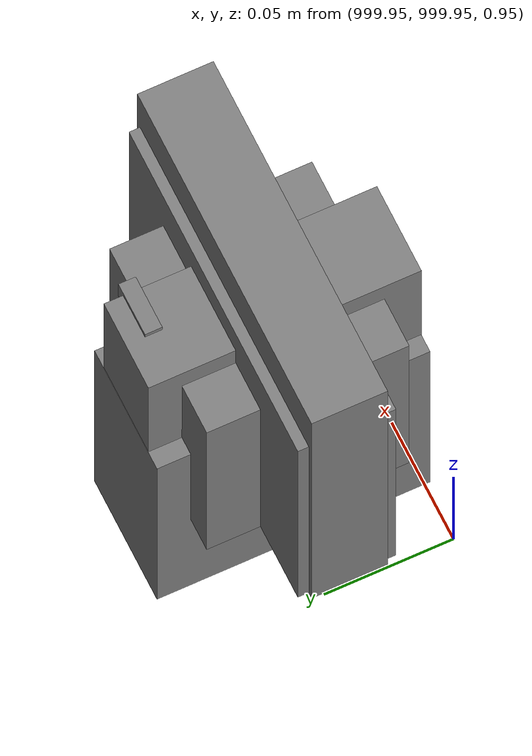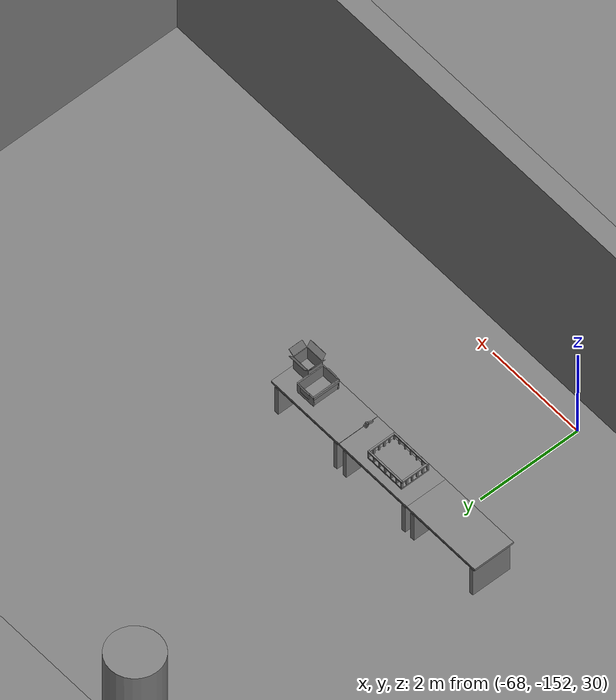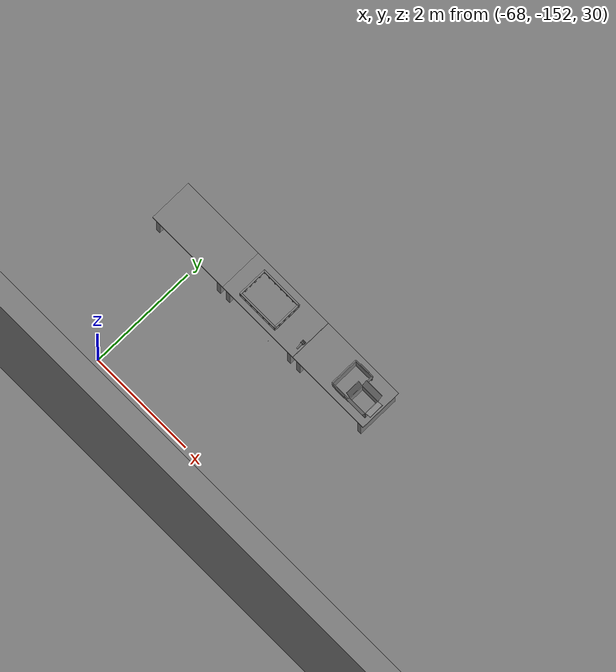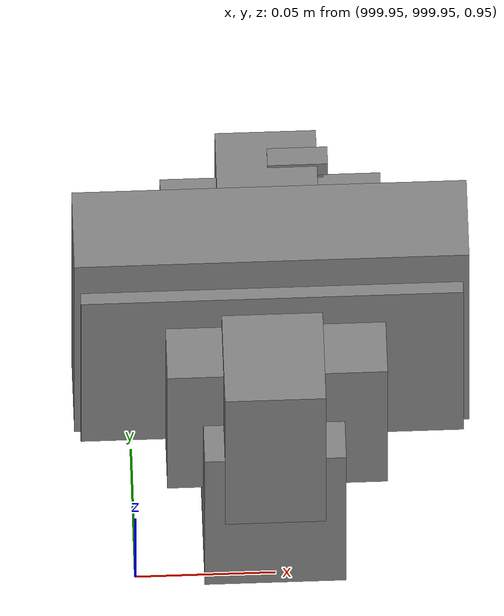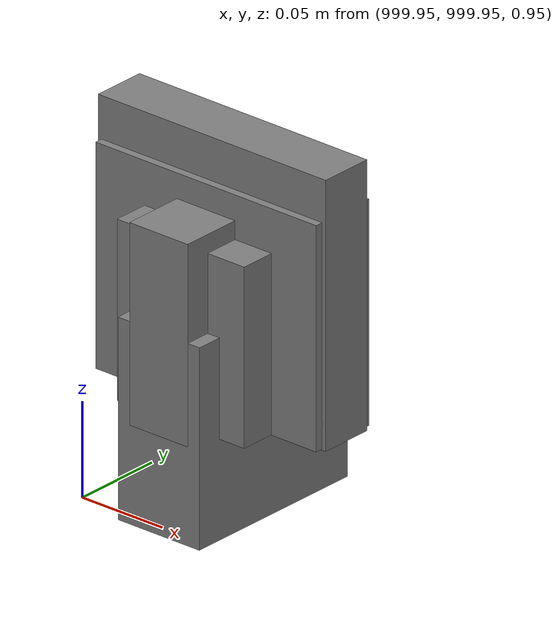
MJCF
<mujoco>
    <option gravity="0.000000000 0.000000000 -9.810000420" timestep="0.0049999999" integrator="implicitfast" density="1.225" viscosity="1.8000001e-05" noslip_iterations="10" iterations="100" sdf_iterations="50">
        <flag multiccd="disable"/>
    </option>
    <size memory="1000M"/>
    <compiler coordinate="local"/>
    <worldbody>
        <light cutoff="30" pos="0 1 1" dir="0 -1 -2"/>
        <light cutoff="30" pos="0 -1 1" dir="0 1 -2"/>
        <body pos="-64.866622925 -149.383972168 30.183746338" euler="89.999984741 89.999946594 0.000000000" name="openloong_gripper_2f85_fix_base_usda_bluebox_01">
            <geom contype="1" conaffinity="1" density="1000" type="box" material="" rgba="0.500000000 0.500000000 0.500000000 1.000000000" solimp="0.899999976 0.949999988 0.001000000" friction="1.000000000 0.005000000 0.000100000" solref="0.020000000 1.000000000" margin="0" condim="3" group="0" pos="0.276580811 0.187225342 0.000068665" quat="0.707106948 0.000077471 0.707106352 0.000077486" size="0.100000001 0.057999998 0.010000000" name="openloong_gripper_2f85_fix_base_usda_geom_E7B7E92E_472B_440E_AF3D_CE4D01F71379"/>
            <geom contype="1" conaffinity="1" density="1000" type="box" material="" rgba="0.500000000 0.500000000 0.500000000 1.000000000" solimp="0.899999976 0.949999988 0.001000000" friction="1.000000000 0.005000000 0.000100000" solref="0.020000000 1.000000000" margin="0" condim="3" group="0" pos="0.000000000 0.002883911 0.000000000" quat="0.999999881 0.000000000 0.000000000 0.000000000" size="0.254000008 0.003000000 0.172000006" name="openloong_gripper_2f85_fix_base_usda_geom_BAC9DAE6_FB67_49B4_AC10_84AA294B668D"/>
            <geom contype="1" conaffinity="1" density="1000" type="box" material="" rgba="0.500000000 0.500000000 0.500000000 1.000000000" solimp="0.899999976 0.949999988 0.001000000" friction="1.000000000 0.005000000 0.000100000" solref="0.020000000 1.000000000" margin="0" condim="3" group="0" pos="0.000000000 0.124874115 0.173484802" quat="0.999796331 0.020176515 -0.000000015 0.000000030" size="0.259999990 0.119999997 0.007000000" name="openloong_gripper_2f85_fix_base_usda_geom_A4C58C89_E325_4CDA_9F16_DAE147BBD97B"/>
            <geom contype="1" conaffinity="1" density="1000" type="box" material="" rgba="0.500000000 0.500000000 0.500000000 1.000000000" solimp="0.899999976 0.949999988 0.001000000" friction="1.000000000 0.005000000 0.000100000" solref="0.020000000 1.000000000" margin="0" condim="3" group="0" pos="0.000000000 0.124874115 -0.173469543" quat="0.999796331 -0.020176545 -0.000000015 0.000000000" size="0.259999990 0.119999997 0.007000000" name="openloong_gripper_2f85_fix_base_usda_geom_DA375039_161B_48B3_9156_A4FE2109A1F5"/>
            <geom contype="1" conaffinity="1" density="1000" type="box" material="" rgba="0.500000000 0.500000000 0.500000000 1.000000000" solimp="0.899999976 0.949999988 0.001000000" friction="1.000000000 0.005000000 0.000100000" solref="0.020000000 1.000000000" margin="0" condim="3" group="0" pos="0.000000000 0.214008331 0.188980103" quat="0.999912977 0.013176724 0.000000015 0.000000000" size="0.259999990 0.029999999 0.012500000" name="openloong_gripper_2f85_fix_base_usda_geom_44188DA1_5ED7_4B3D_8475_25FADF612F06"/>
            <geom contype="1" conaffinity="1" density="1000" type="box" material="" rgba="0.500000000 0.500000000 0.500000000 1.000000000" solimp="0.899999976 0.949999988 0.001000000" friction="1.000000000 0.005000000 0.000100000" solref="0.020000000 1.000000000" margin="0" condim="3" group="0" pos="-0.258361816 0.125289917 0.001876831" quat="0.702796936 -0.020792112 0.710783124 0.020769298" size="0.189999998 0.119999997 0.009000000" name="openloong_gripper_2f85_fix_base_usda_geom_2D4EF5C2_4C56_4036_A886_97989BA8A04A"/>
            <geom contype="1" conaffinity="1" density="1000" type="box" material="" rgba="0.500000000 0.500000000 0.500000000 1.000000000" solimp="0.899999976 0.949999988 0.001000000" friction="1.000000000 0.005000000 0.000100000" solref="0.020000000 1.000000000" margin="0" condim="3" group="0" pos="0.000000000 0.214008331 -0.188980103" quat="0.999912977 -0.013176769 0.000000030 0.000000015" size="0.259999990 0.029999999 0.012500000" name="openloong_gripper_2f85_fix_base_usda_geom_5CA7FDE6_5829_43E9_9B46_0D4F0F39778F"/>
            <geom contype="1" conaffinity="1" density="1000" type="box" material="" rgba="0.500000000 0.500000000 0.500000000 1.000000000" solimp="0.899999976 0.949999988 0.001000000" friction="1.000000000 0.005000000 0.000100000" solref="0.020000000 1.000000000" margin="0" condim="3" group="0" pos="-0.276611328 0.187225342 0.000068665" quat="0.707106650 0.000077441 0.707106709 0.000077456" size="0.100000001 0.057999998 0.010000000" name="openloong_gripper_2f85_fix_base_usda_geom_0A9728E1_F761_446A_A783_6B7B7FF2BEF0"/>
            <geom contype="1" conaffinity="1" density="1000" type="box" material="" rgba="0.500000000 0.500000000 0.500000000 1.000000000" solimp="0.899999976 0.949999988 0.001000000" friction="1.000000000 0.005000000 0.000100000" solref="0.020000000 1.000000000" margin="0" condim="3" group="0" pos="0.258331299 0.125289917 0.001876831" quat="0.702851415 0.018856421 0.710823774 -0.019329369" size="0.189999998 0.119999997 0.009000000" name="openloong_gripper_2f85_fix_base_usda_geom_788EE435_4503_466A_8A94_9F9DBE4BB692"/>
            <freejoint name="openloong_gripper_2f85_fix_base_usda_bluebox_01_joint"/>
            <site size="0.005000000 0.005000000 0.005000000" rgba="0.500000000 0.500000000 0.500000000 1.000000000" pos="0.000000000 0.000000000 0.000000000" quat="0.999961913 0.008726534 0.000000000 0.000000000" group="0" type="sphere" name="openloong_gripper_2f85_fix_base_usda_bluebox_01site"/>
        </body>
        <body pos="-64.496299744 -149.491867065 30.235729218" euler="0.000000000 0.000000000 89.999946594" name="openloong_gripper_2f85_fix_base_usda_cardboardbox_01">
            <geom contype="1" conaffinity="1" density="1000" type="box" material="" rgba="0.500000000 0.500000000 0.500000000 1.000000000" solimp="0.899999976 0.949999988 0.001000000" friction="1.000000000 0.005000000 0.000100000" solref="0.020000000 1.000000000" margin="0" condim="3" group="0" pos="-0.003166199 -0.004086494 0.005052090" quat="1.000000000 0.000000000 0.000000000 0.000000000" size="0.142499998 0.177500010 0.005000000" name="openloong_gripper_2f85_fix_base_usda_geom_2C49248F_4E4F_486C_8FE8_891EB644B7BA"/>
            <geom contype="1" conaffinity="1" density="1000" type="box" material="" rgba="0.500000000 0.500000000 0.500000000 1.000000000" solimp="0.899999976 0.949999988 0.001000000" friction="1.000000000 0.005000000 0.000100000" solref="0.020000000 1.000000000" margin="0" condim="3" group="0" pos="-0.003166199 0.170316696 0.150570869" quat="1.000000000 0.000000000 0.000000000 0.000000000" size="0.142499998 0.005000000 0.149999991" name="openloong_gripper_2f85_fix_base_usda_geom_E84F1D60_EA82_43E2_8D09_A33B1859467A"/>
            <geom contype="1" conaffinity="1" density="1000" type="box" material="" rgba="0.500000000 0.500000000 0.500000000 1.000000000" solimp="0.899999976 0.949999988 0.001000000" friction="1.000000000 0.005000000 0.000100000" solref="0.020000000 1.000000000" margin="0" condim="3" group="0" pos="-0.147399902 -0.005307198 0.150570869" quat="1.000000000 0.000000000 0.000000000 0.000000000" size="0.005000000 0.177500010 0.149999991" name="openloong_gripper_2f85_fix_base_usda_geom_D3CC6D89_6037_4288_94AF_073DBA3BB0D0"/>
            <geom contype="1" conaffinity="1" density="1000" type="box" material="" rgba="0.500000000 0.500000000 0.500000000 1.000000000" solimp="0.899999976 0.949999988 0.001000000" friction="1.000000000 0.005000000 0.000100000" solref="0.020000000 1.000000000" margin="0" condim="3" group="0" pos="0.140275955 -0.005307198 0.150570869" quat="1.000000000 0.000000000 0.000000000 0.000000000" size="0.005000000 0.177500010 0.149999991" name="openloong_gripper_2f85_fix_base_usda_geom_C0A605E1_711F_4CDE_A0D2_512F3D646449"/>
            <geom contype="1" conaffinity="1" density="1000" type="box" material="" rgba="0.500000000 0.500000000 0.500000000 1.000000000" solimp="0.899999976 0.949999988 0.001000000" friction="1.000000000 0.005000000 0.000100000" solref="0.020000000 1.000000000" margin="0" condim="3" group="0" pos="-0.003166199 -0.181550980 0.150570869" quat="1.000000000 0.000000000 0.000000000 0.000000000" size="0.142499998 0.005000000 0.149999991" name="openloong_gripper_2f85_fix_base_usda_geom_D1CB8FFF_959B_4122_A7CA_4D86A04FC7EF"/>
            <freejoint name="openloong_gripper_2f85_fix_base_usda_cardboardbox_01_joint"/>
            <site size="0.005000000 0.005000000 0.005000000" rgba="0.500000000 0.500000000 0.500000000 1.000000000" pos="0.000000000 0.000000000 0.000000000" quat="0.999961913 0.008726535 0.000000000 0.000000000" group="0" type="sphere" name="openloong_gripper_2f85_fix_base_usda_site_72DD4591_3B38_46F7_9E24_692856E49625"/>
            <body pos="0.139160156 -0.004048347 0.301930904" euler="-179.999954224 49.383502960 179.999954224" name="openloong_gripper_2f85_fix_base_usda_A1_006">
                <geom contype="1" conaffinity="1" density="1000" type="box" material="" rgba="0.500000000 0.500000000 0.500000000 1.000000000" solimp="0.899999976 0.949999988 0.001000000" friction="1.000000000 0.005000000 0.000100000" solref="0.020000000 1.000000000" margin="0" condim="3" group="0" pos="-0.071587563 0.000009537 0.001745224" quat="0.999999881 0.000000000 0.000000000 0.000000000" size="0.071249999 0.179999992 0.002500000" name="openloong_gripper_2f85_fix_base_usda_geom_39201DE5_B871_42A2_8C51_8DCC7590D14B"/>
                <joint armature="0" stiffness="0.07" damping="0.0099999998" axis="0.000000 1.000000 0.000000" type="hinge" name="openloong_gripper_2f85_fix_base_usda_A1_006"/>
            </body>
            <body pos="-0.145902634 -0.004086494 0.301938057" euler="-180.000000000 -60.000011444 -180.000000000" name="openloong_gripper_2f85_fix_base_usda_A2_006">
                <geom contype="1" conaffinity="1" density="1000" type="box" material="" rgba="0.500000000 0.500000000 0.500000000 1.000000000" solimp="0.899999976 0.949999988 0.001000000" friction="1.000000000 0.005000000 0.000100000" solref="0.020000000 1.000000000" margin="0" condim="3" group="0" pos="0.071268082 0.000009537 0.002717972" quat="0.000002921 0.000000000 -0.000000030 0.999999881" size="0.071249999 0.179999992 0.002500000" name="openloong_gripper_2f85_fix_base_usda_geom_A0104C1D_B33D_444B_9A31_F8A9A2E5E3F0"/>
                <joint armature="0" stiffness="0.07" damping="0.0099999998" axis="0.000000 1.000000 0.000000" type="hinge" name="openloong_gripper_2f85_fix_base_usda_A2_006"/>
            </body>
            <body pos="-0.003385544 0.175991058 0.301930904" euler="-125.858116150 -0.000004561 0.000002331" name="openloong_gripper_2f85_fix_base_usda_B2_006">
                <geom contype="1" conaffinity="1" density="1000" type="box" material="" rgba="0.500000000 0.500000000 0.500000000 1.000000000" solimp="0.899999976 0.949999988 0.001000000" friction="1.000000000 0.005000000 0.000100000" solref="0.020000000 1.000000000" margin="0" condim="3" group="0" pos="0.000009537 -0.070939064 -0.002470016" quat="0.999614120 0.027776197 -0.000000015 0.000000030" size="0.137500003 0.064999998 0.005000000" name="openloong_gripper_2f85_fix_base_usda_geom_24FB9660_E0A6_4A9D_9332_A886E49A3A6A"/>
                <joint armature="0" stiffness="0.07" damping="0.0099999998" axis="1.000000 0.000000 0.000000" type="hinge" name="openloong_gripper_2f85_fix_base_usda_B2_006"/>
            </body>
            <body pos="-0.003385544 -0.184140205 0.301938057" euler="147.805557251 0.000000000 0.000000000" name="openloong_gripper_2f85_fix_base_usda_B1_006">
                <geom contype="1" conaffinity="1" density="1000" type="box" material="" rgba="0.500000000 0.500000000 0.500000000 1.000000000" solimp="0.899999976 0.949999988 0.001000000" friction="1.000000000 0.005000000 0.000100000" solref="0.020000000 1.000000000" margin="0" condim="3" group="0" pos="-0.000028610 0.070202351 -0.002703667" quat="0.999614179 -0.027776167 0.000000000 0.000000000" size="0.137500003 0.064999998 0.005000000" name="openloong_gripper_2f85_fix_base_usda_geom_DBAE39BA_EEE2_47B1_A4E9_EEE1EAD0502D"/>
                <joint armature="0" stiffness="0.07" damping="0.0099999998" axis="1.000000 0.000000 0.000000" type="hinge" name="openloong_gripper_2f85_fix_base_usda_B1_006"/>
            </body>
        </body>
        <body pos="-65.882858276 -149.481979370 30.229999542" euler="-64.487716675 0.000000000 0.000000000" name="openloong_gripper_2f85_fix_base_usda_Barcode">
            <geom contype="1" conaffinity="1" density="1000" type="box" material="" rgba="0.500000000 0.500000000 0.500000000 1.000000000" solimp="0.899999976 0.949999988 0.001000000" friction="1.000000000 0.005000000 0.000100000" solref="0.020000000 1.000000000" margin="0" condim="3" group="0" pos="0.000000000 0.013038635 0.001419067" quat="0.000000000 0.000000000 0.000000000 1.000000119" size="0.034000002 0.010000000 0.017999999" name="openloong_gripper_2f85_fix_base_usda_geom_CF8ED020_D6A3_4212_B5F4_003863B73878"/>
            <geom contype="1" conaffinity="1" density="1000" type="box" material="" rgba="0.500000000 0.500000000 0.500000000 1.000000000" solimp="0.899999976 0.949999988 0.001000000" friction="1.000000000 0.005000000 0.000100000" solref="0.020000000 1.000000000" margin="0" condim="3" group="0" pos="0.000000000 -0.035301208 -0.007095337" quat="0.000000000 0.000000000 -0.043619365 0.999048233" size="0.028999999 0.010000000 0.020000000" name="openloong_gripper_2f85_fix_base_usda_geom_1B999B41_A1FD_4389_88AD_6C9A37FE8B46"/>
            <geom contype="1" conaffinity="1" density="1000" type="box" material="" rgba="0.500000000 0.500000000 0.500000000 1.000000000" solimp="0.899999976 0.949999988 0.001000000" friction="1.000000000 0.005000000 0.000100000" solref="0.020000000 1.000000000" margin="0" condim="3" group="0" pos="0.000000000 -0.043411255 -0.011749268" quat="0.922262907 0.386563420 0.000000000 0.000000000" size="0.026000001 0.010000000 0.020000000" name="openloong_gripper_2f85_fix_base_usda_geom_65D55038_CE18_4E91_9F2B_EE1C8BA87B05"/>
            <geom contype="1" conaffinity="1" density="1000" type="box" material="" rgba="0.500000000 0.500000000 0.500000000 1.000000000" solimp="0.899999976 0.949999988 0.001000000" friction="1.000000000 0.005000000 0.000100000" solref="0.020000000 1.000000000" margin="0" condim="3" group="0" pos="0.000000000 -0.016967773 -0.031860352" quat="0.000000000 0.000000000 0.000000000 1.000000119" size="0.008000000 0.010000000 0.013000000" name="openloong_gripper_2f85_fix_base_usda_geom_4CC9A78E_0252_42B3_8FFD_BD272FC5EBDD"/>
            <geom contype="1" conaffinity="1" density="1000" type="box" material="" rgba="0.500000000 0.500000000 0.500000000 1.000000000" solimp="0.899999976 0.949999988 0.001000000" friction="1.000000000 0.005000000 0.000100000" solref="0.020000000 1.000000000" margin="0" condim="3" group="0" pos="0.000000000 -0.001869202 0.000312805" quat="0.953716993 0.300705761 0.000000000 0.000000000" size="0.032000002 0.010000000 0.018999999" name="openloong_gripper_2f85_fix_base_usda_geom_6DC62982_7CA5_4F6A_B0EC_3A8BB013ABFB"/>
            <geom contype="1" conaffinity="1" density="1000" type="box" material="" rgba="0.500000000 0.500000000 0.500000000 1.000000000" solimp="0.899999976 0.949999988 0.001000000" friction="1.000000000 0.005000000 0.000100000" solref="0.020000000 1.000000000" margin="0" condim="3" group="0" pos="0.000000000 -0.019531250 -0.003173828" quat="0.953716993 0.300705761 0.000000000 0.000000000" size="0.030999999 0.010000000 0.020000000" name="openloong_gripper_2f85_fix_base_usda_geom_6BB89009_F25A_4A06_8C3F_5DCC9C65FAC0"/>
            <geom contype="1" conaffinity="1" density="1000" type="box" material="" rgba="0.500000000 0.500000000 0.500000000 1.000000000" solimp="0.899999976 0.949999988 0.001000000" friction="1.000000000 0.005000000 0.000100000" solref="0.020000000 1.000000000" margin="0" condim="3" group="0" pos="0.000000000 -0.035301208 -0.007095337" quat="0.953716993 0.300705761 0.000000000 0.000000000" size="0.028999999 0.010000000 0.020000000" name="openloong_gripper_2f85_fix_base_usda_geom_55F0D4AE_1E2D_4C87_92D9_28CD52A15D0D"/>
            <geom contype="1" conaffinity="1" density="1000" type="box" material="" rgba="0.500000000 0.500000000 0.500000000 1.000000000" solimp="0.899999976 0.949999988 0.001000000" friction="1.000000000 0.005000000 0.000100000" solref="0.020000000 1.000000000" margin="0" condim="3" group="0" pos="0.000000000 -0.042617798 -0.071121216" quat="0.000000000 0.000000000 0.000000000 1.000000119" size="0.013000000 0.021000000 0.059999999" name="openloong_gripper_2f85_fix_base_usda_geom_F12E7422_DC1A_4784_9D86_713F3EB31218"/>
            <freejoint name="openloong_gripper_2f85_fix_base_usda_Barcode_joint"/>
            <site size="0.005000000 0.005000000 0.005000000" rgba="0.500000000 0.500000000 0.500000000 1.000000000" pos="0.000000000 0.000000000 0.000000000" quat="1.000000000 0.000000000 0.000000000 0.000000000" group="0" type="sphere" name="openloong_gripper_2f85_fix_base_usda_Barcode_site"/>
        </body>
        <body pos="-66.745018005 -149.392349243 30.184000015" euler="0.000000000 0.000000000 89.999946594" name="[22330468611293]_Basket_01">
            <geom contype="1" conaffinity="1" density="1000" type="box" material="" rgba="0.500000000 0.500000000 0.500000000 1.000000000" solimp="0.899999976 0.949999988 0.001000000" friction="1.000000000 0.005000000 0.000100000" solref="0.020000000 1.000000000" margin="0" condim="3" group="0" pos="-0.052425385 0.389207840 0.089787483" quat="0.707107008 0.000000000 0.000000000 0.707106411" size="0.014249999 0.014249999 0.059999999" name="[22330468611293]_geom_F81248BF_848B_401B_872D_76B7D02AFD92"/>
            <geom contype="1" conaffinity="1" density="1000" type="box" material="" rgba="0.500000000 0.500000000 0.500000000 1.000000000" solimp="0.899999976 0.949999988 0.001000000" friction="1.000000000 0.005000000 0.000100000" solref="0.020000000 1.000000000" margin="0" condim="3" group="0" pos="0.264015198 -0.133043289 0.089787483" quat="0.707107008 0.000000000 0.000000000 0.707106411" size="0.014249999 0.014249999 0.059999999" name="[22330468611293]_geom_3C619502_1FE8_4167_AD6B_41B16F121711"/>
            <geom contype="1" conaffinity="1" density="1000" type="box" material="" rgba="0.500000000 0.500000000 0.500000000 1.000000000" solimp="0.899999976 0.949999988 0.001000000" friction="1.000000000 0.005000000 0.000100000" solref="0.020000000 1.000000000" margin="0" condim="3" group="0" pos="-0.264015198 -0.265548706 0.089793205" quat="0.707107008 0.000000000 0.000000000 0.707106411" size="0.014249999 0.014249999 0.059999999" name="[22330468611293]_geom_249E681D_75E9_4700_91A2_8027048D290F"/>
            <geom contype="1" conaffinity="1" density="1000" type="box" material="" rgba="0.500000000 0.500000000 0.500000000 1.000000000" solimp="0.899999976 0.949999988 0.001000000" friction="1.000000000 0.005000000 0.000100000" solref="0.020000000 1.000000000" margin="0" condim="3" group="0" pos="-0.160263062 -0.389322281 0.089793205" quat="0.707107008 0.000000000 0.000000000 0.707106411" size="0.014249999 0.014249999 0.059999999" name="[22330468611293]_geom_5CB5EA2B_BC17_4269_84CA_BC512CF0A39D"/>
            <geom contype="1" conaffinity="1" density="1000" type="box" material="" rgba="0.500000000 0.500000000 0.500000000 1.000000000" solimp="0.899999976 0.949999988 0.001000000" friction="1.000000000 0.005000000 0.000100000" solref="0.020000000 1.000000000" margin="0" condim="3" group="0" pos="0.162265778 -0.389322281 0.089787483" quat="0.707107008 0.000000000 0.000000000 0.707106411" size="0.014249999 0.014249999 0.059999999" name="[22330468611293]_geom_295A6CCF_C1C5_421B_8C37_1AED236D0EC4"/>
            <geom contype="1" conaffinity="1" density="1000" type="box" material="" rgba="0.500000000 0.500000000 0.500000000 1.000000000" solimp="0.899999976 0.949999988 0.001000000" friction="1.000000000 0.005000000 0.000100000" solref="0.020000000 1.000000000" margin="0" condim="3" group="0" pos="0.264015198 0.389207840 0.089787483" quat="0.707107008 0.000000000 0.000000000 0.707106411" size="0.014249999 0.014249999 0.059999999" name="[22330468611293]_geom_1A4E4557_179B_4369_B81C_5366DAE22D6C"/>
            <geom contype="1" conaffinity="1" density="1000" type="box" material="" rgba="0.500000000 0.500000000 0.500000000 1.000000000" solimp="0.899999976 0.949999988 0.001000000" friction="1.000000000 0.005000000 0.000100000" solref="0.020000000 1.000000000" margin="0" condim="3" group="0" pos="-0.264015198 -0.133043289 0.089793205" quat="0.707107008 0.000000000 0.000000000 0.707106411" size="0.014249999 0.014249999 0.059999999" name="[22330468611293]_geom_083BCF4A_9A35_49A9_A5F6_6E71CEA19B01"/>
            <geom contype="1" conaffinity="1" density="1000" type="box" material="" rgba="0.500000000 0.500000000 0.500000000 1.000000000" solimp="0.899999976 0.949999988 0.001000000" friction="1.000000000 0.005000000 0.000100000" solref="0.020000000 1.000000000" margin="0" condim="3" group="0" pos="-0.264026642 0.269256592 0.089793205" quat="0.707107008 0.000000000 0.000000000 0.707106411" size="0.014249999 0.014249999 0.059999999" name="[22330468611293]_geom_99B19076_7EBE_4C8A_B205_D143567FBA19"/>
            <geom contype="1" conaffinity="1" density="1000" type="box" material="" rgba="0.500000000 0.500000000 0.500000000 1.000000000" solimp="0.899999976 0.949999988 0.001000000" friction="1.000000000 0.005000000 0.000100000" solref="0.020000000 1.000000000" margin="0" condim="3" group="0" pos="0.054462433 0.389207840 0.089787483" quat="0.707107008 0.000000000 0.000000000 0.707106411" size="0.014249999 0.014249999 0.059999999" name="[22330468611293]_geom_FF8DC096_5A41_46FE_AE41_2644A3897A0E"/>
            <geom contype="1" conaffinity="1" density="1000" type="box" material="" rgba="0.500000000 0.500000000 0.500000000 1.000000000" solimp="0.899999976 0.949999988 0.001000000" friction="1.000000000 0.005000000 0.000100000" solref="0.020000000 1.000000000" margin="0" condim="3" group="0" pos="0.054462433 -0.389322281 0.089787483" quat="0.707107008 0.000000000 0.000000000 0.707106411" size="0.014249999 0.014249999 0.059999999" name="[22330468611293]_geom_F1AA9DF8_6DAD_4D26_9380_278BA0742B07"/>
            <geom contype="1" conaffinity="1" density="1000" type="box" material="" rgba="0.500000000 0.500000000 0.500000000 1.000000000" solimp="0.899999976 0.949999988 0.001000000" friction="1.000000000 0.005000000 0.000100000" solref="0.020000000 1.000000000" margin="0" condim="3" group="0" pos="0.264015198 0.269256592 0.089793205" quat="0.707107008 0.000000000 0.000000000 0.707106411" size="0.014249999 0.014249999 0.059999999" name="[22330468611293]_geom_AF86CFBE_20DE_4F89_88BD_06AD9659D565"/>
            <geom contype="1" conaffinity="1" density="1000" type="box" material="" rgba="0.500000000 0.500000000 0.500000000 1.000000000" solimp="0.899999976 0.949999988 0.001000000" friction="1.000000000 0.005000000 0.000100000" solref="0.020000000 1.000000000" margin="0" condim="3" group="0" pos="0.264015198 -0.389322281 0.089787483" quat="0.707107008 0.000000000 0.000000000 0.707106411" size="0.014249999 0.014249999 0.059999999" name="[22330468611293]_geom_2A8EF748_B6AC_4356_81FB_27BC7A719F41"/>
            <geom contype="1" conaffinity="1" density="1000" type="box" material="" rgba="0.500000000 0.500000000 0.500000000 1.000000000" solimp="0.899999976 0.949999988 0.001000000" friction="1.000000000 0.005000000 0.000100000" solref="0.020000000 1.000000000" margin="0" condim="3" group="0" pos="0.000000000 0.000000000 0.015998840" quat="0.707107008 0.000000000 0.000000000 0.707106411" size="0.403499991 0.279000014 0.015750000" name="[22330468611293]_geom_F442BCA2_C11D_4319_ABDB_64C02166028E"/>
            <geom contype="1" conaffinity="1" density="1000" type="box" material="" rgba="0.500000000 0.500000000 0.500000000 1.000000000" solimp="0.899999976 0.949999988 0.001000000" friction="1.000000000 0.005000000 0.000100000" solref="0.020000000 1.000000000" margin="0" condim="3" group="0" pos="0.000000000 -0.389476776 0.163619041" quat="0.707107008 0.000000000 0.000000000 0.707106411" size="0.015000000 0.277500004 0.015750000" name="[22330468611293]_geom_7AF9AB99_80CC_4921_ABD4_7615CBF26668"/>
            <geom contype="1" conaffinity="1" density="1000" type="box" material="" rgba="0.500000000 0.500000000 0.500000000 1.000000000" solimp="0.899999976 0.949999988 0.001000000" friction="1.000000000 0.005000000 0.000100000" solref="0.020000000 1.000000000" margin="0" condim="3" group="0" pos="0.162265778 0.389207840 0.089787483" quat="0.707107008 0.000000000 0.000000000 0.707106411" size="0.014249999 0.014249999 0.059999999" name="[22330468611293]_geom_56E02734_5419_436D_94AB_B200FB9CBEA0"/>
            <geom contype="1" conaffinity="1" density="1000" type="box" material="" rgba="0.500000000 0.500000000 0.500000000 1.000000000" solimp="0.899999976 0.949999988 0.001000000" friction="1.000000000 0.005000000 0.000100000" solref="0.020000000 1.000000000" margin="0" condim="3" group="0" pos="0.000000000 0.389471054 0.163619041" quat="0.707107008 0.000000000 0.000000000 0.707106411" size="0.015000000 0.277500004 0.015750000" name="[22330468611293]_geom_A8920224_FEB6_41D7_AAED_47A623A25686"/>
            <geom contype="1" conaffinity="1" density="1000" type="box" material="" rgba="0.500000000 0.500000000 0.500000000 1.000000000" solimp="0.899999976 0.949999988 0.001000000" friction="1.000000000 0.005000000 0.000100000" solref="0.020000000 1.000000000" margin="0" condim="3" group="0" pos="-0.263511658 0.000000000 0.163619041" quat="0.707107008 0.000000000 0.000000000 0.707106411" size="0.403499991 0.015000000 0.015750000" name="[22330468611293]_geom_02F4E429_D953_4C6A_AABB_0F1DC6896AC0"/>
            <geom contype="1" conaffinity="1" density="1000" type="box" material="" rgba="0.500000000 0.500000000 0.500000000 1.000000000" solimp="0.899999976 0.949999988 0.001000000" friction="1.000000000 0.005000000 0.000100000" solref="0.020000000 1.000000000" margin="0" condim="3" group="0" pos="-0.264015198 0.141334534 0.089793205" quat="0.707107008 0.000000000 0.000000000 0.707106411" size="0.014249999 0.014249999 0.059999999" name="[22330468611293]_geom_364BB4B3_927C_4595_877A_F216690BCC11"/>
            <geom contype="1" conaffinity="1" density="1000" type="box" material="" rgba="0.500000000 0.500000000 0.500000000 1.000000000" solimp="0.899999976 0.949999988 0.001000000" friction="1.000000000 0.005000000 0.000100000" solref="0.020000000 1.000000000" margin="0" condim="3" group="0" pos="0.264015198 -0.265548706 0.089787483" quat="0.707107008 0.000000000 0.000000000 0.707106411" size="0.014249999 0.014249999 0.059999999" name="[22330468611293]_geom_D923E6D0_6CD8_4560_AA3D_F6034A3A0119"/>
            <geom contype="1" conaffinity="1" density="1000" type="box" material="" rgba="0.500000000 0.500000000 0.500000000 1.000000000" solimp="0.899999976 0.949999988 0.001000000" friction="1.000000000 0.005000000 0.000100000" solref="0.020000000 1.000000000" margin="0" condim="3" group="0" pos="-0.160263062 0.389207840 0.089787483" quat="0.707107008 0.000000000 0.000000000 0.707106411" size="0.014249999 0.014249999 0.059999999" name="[22330468611293]_geom_524A91CB_FAA4_4CA6_A321_A2C3D9E0052B"/>
            <geom contype="1" conaffinity="1" density="1000" type="box" material="" rgba="0.500000000 0.500000000 0.500000000 1.000000000" solimp="0.899999976 0.949999988 0.001000000" friction="1.000000000 0.005000000 0.000100000" solref="0.020000000 1.000000000" margin="0" condim="3" group="0" pos="-0.052425385 -0.389322281 0.089787483" quat="0.707107008 0.000000000 0.000000000 0.707106411" size="0.014249999 0.014249999 0.059999999" name="[22330468611293]_geom_32437F85_05E0_4F8E_A1DB_CE18D054E6E2"/>
            <geom contype="1" conaffinity="1" density="1000" type="box" material="" rgba="0.500000000 0.500000000 0.500000000 1.000000000" solimp="0.899999976 0.949999988 0.001000000" friction="1.000000000 0.005000000 0.000100000" solref="0.020000000 1.000000000" margin="0" condim="3" group="0" pos="-0.264026642 -0.389322281 0.089793205" quat="0.707107008 0.000000000 0.000000000 0.707106411" size="0.014249999 0.014249999 0.059999999" name="[22330468611293]_geom_81C68B1C_AFD5_48FB_87C8_D3C662CC3ECD"/>
            <geom contype="1" conaffinity="1" density="1000" type="box" material="" rgba="0.500000000 0.500000000 0.500000000 1.000000000" solimp="0.899999976 0.949999988 0.001000000" friction="1.000000000 0.005000000 0.000100000" solref="0.020000000 1.000000000" margin="0" condim="3" group="0" pos="0.264015198 0.141334534 0.089787483" quat="0.707107008 0.000000000 0.000000000 0.707106411" size="0.014249999 0.014249999 0.059999999" name="[22330468611293]_geom_C85AE0C0_D2B5_4FEB_937C_E349D41E5E8E"/>
            <geom contype="1" conaffinity="1" density="1000" type="box" material="" rgba="0.500000000 0.500000000 0.500000000 1.000000000" solimp="0.899999976 0.949999988 0.001000000" friction="1.000000000 0.005000000 0.000100000" solref="0.020000000 1.000000000" margin="0" condim="3" group="0" pos="-0.264015198 0.389207840 0.089793205" quat="0.707107008 0.000000000 0.000000000 0.707106411" size="0.014249999 0.014249999 0.059999999" name="[22330468611293]_geom_BE9651EE_571B_4726_8379_71A9678D26E3"/>
            <geom contype="1" conaffinity="1" density="1000" type="box" material="" rgba="0.500000000 0.500000000 0.500000000 1.000000000" solimp="0.899999976 0.949999988 0.001000000" friction="1.000000000 0.005000000 0.000100000" solref="0.020000000 1.000000000" margin="0" condim="3" group="0" pos="0.264015198 0.004480362 0.089787483" quat="0.707107008 0.000000000 0.000000000 0.707106411" size="0.014249999 0.014249999 0.059999999" name="[22330468611293]_geom_E22C6349_C5BA_4C46_A284_D01A727BBE06"/>
            <geom contype="1" conaffinity="1" density="1000" type="box" material="" rgba="0.500000000 0.500000000 0.500000000 1.000000000" solimp="0.899999976 0.949999988 0.001000000" friction="1.000000000 0.005000000 0.000100000" solref="0.020000000 1.000000000" margin="0" condim="3" group="0" pos="0.263694763 -0.000011444 0.163619041" quat="0.707107008 0.000000000 0.000000000 0.707106411" size="0.403499991 0.015000000 0.015750000" name="[22330468611293]_geom_6009D766_5484_464C_A266_C9B018E27DA2"/>
            <geom contype="1" conaffinity="1" density="1000" type="box" material="" rgba="0.500000000 0.500000000 0.500000000 1.000000000" solimp="0.899999976 0.949999988 0.001000000" friction="1.000000000 0.005000000 0.000100000" solref="0.020000000 1.000000000" margin="0" condim="3" group="0" pos="-0.264015198 0.004480362 0.089793205" quat="0.707107008 0.000000000 0.000000000 0.707106411" size="0.014249999 0.014249999 0.059999999" name="[22330468611293]_geom_B9DD0390_32E1_45F6_967B_5DD8E7B7E97F"/>
            <freejoint name="[22330468611293]_joint_EFD9DCAB_CCB8_4E3E_A607_9956CB0BBAB8"/>
        </body>
        <body pos="0.000000000 0.000000000 0.000000000" euler="0.000000000 0.000000000 0.000000000" name="Static Objects_Static Objects">
            <geom contype="1" conaffinity="1" density="1000" type="box" material="" rgba="0.500000000 0.500000000 0.500000000 1.000000000" solimp="0.899999976 0.949999988 0.001000000" friction="1.000000000 0.005000000 0.000100000" solref="0.020000000 1.000000000" margin="0" condim="3" group="0" pos="-67.544113159 -149.365814209 29.727830887" quat="0.500000417 0.499999970 0.499999553 0.499999970" size="0.381000012 0.319999993 0.041000001" name="Static Objects_geom_85C9D3AD_567D_4894_A881_AFCBFFDA0754"/>
            <geom contype="1" conaffinity="1" density="1000" type="box" material="" rgba="0.500000000 0.500000000 0.500000000 1.000000000" solimp="0.899999976 0.949999988 0.001000000" friction="1.000000000 0.005000000 0.000100000" solref="0.020000000 1.000000000" margin="0" condim="3" group="0" pos="-68.239501953 -149.365814209 30.086868286" quat="0.500000417 0.499999970 0.499999553 0.499999970" size="0.370999992 0.039500002 0.745000005" name="Static Objects_geom_DB812C86_0CA1_4789_933F_E1B95EBA0E56"/>
            <geom contype="1" conaffinity="1" density="1000" type="box" material="" rgba="0.500000000 0.500000000 0.500000000 1.000000000" solimp="0.899999976 0.949999988 0.001000000" friction="1.000000000 0.005000000 0.000100000" solref="0.020000000 1.000000000" margin="0" condim="3" group="0" pos="-68.239501953 -149.365814209 30.147235870" quat="0.500000417 0.499999970 0.499999553 0.499999970" size="0.400000006 0.022000000 0.800000012" name="Static Objects_geom_74477C58_5C6C_483D_B761_CF8916F17620"/>
            <geom contype="1" conaffinity="1" density="1000" type="box" material="" rgba="0.500000000 0.500000000 0.500000000 1.000000000" solimp="0.899999976 0.949999988 0.001000000" friction="1.000000000 0.005000000 0.000100000" solref="0.020000000 1.000000000" margin="0" condim="3" group="0" pos="-68.934890747 -149.365814209 29.727830887" quat="0.500000417 0.499999970 0.499999553 0.499999970" size="0.381000012 0.319999993 0.041000001" name="Static Objects_geom_455F1576_9FD6_4A70_BA3B_5FFC8329F0F7"/>
            <geom contype="1" conaffinity="1" density="1000" type="box" material="" rgba="0.500000000 0.500000000 0.500000000 1.000000000" solimp="0.899999976 0.949999988 0.001000000" friction="1.000000000 0.005000000 0.000100000" solref="0.020000000 1.000000000" margin="0" condim="3" group="0" pos="-68.239501953 -149.365814209 29.561563492" quat="0.500000417 0.499999970 0.499999553 0.499999970" size="0.020000000 0.022000000 0.660000026" name="Static Objects_geom_2E837C33_F28C_4339_B7AE_0BFD1823046B"/>
            <geom contype="1" conaffinity="1" density="1000" type="box" material="" rgba="0.500000000 0.500000000 0.500000000 1.000000000" solimp="0.899999976 0.949999988 0.001000000" friction="1.000000000 0.005000000 0.000100000" solref="0.020000000 1.000000000" margin="0" condim="3" group="0" pos="-65.945671082 -149.365814209 29.727830887" quat="0.500000417 0.499999970 0.499999553 0.499999970" size="0.381000012 0.319999993 0.041000001" name="Static Objects_geom_34F6B1E3_34D0_4538_8DE4_36573986CB81"/>
            <geom contype="1" conaffinity="1" density="1000" type="box" material="" rgba="0.500000000 0.500000000 0.500000000 1.000000000" solimp="0.899999976 0.949999988 0.001000000" friction="1.000000000 0.005000000 0.000100000" solref="0.020000000 1.000000000" margin="0" condim="3" group="0" pos="-66.641059875 -149.365814209 30.086868286" quat="0.500000417 0.499999970 0.499999553 0.499999970" size="0.370999992 0.039500002 0.745000005" name="Static Objects_geom_3F405A48_BEFE_4178_B466_05748FC8FA19"/>
            <geom contype="1" conaffinity="1" density="1000" type="box" material="" rgba="0.500000000 0.500000000 0.500000000 1.000000000" solimp="0.899999976 0.949999988 0.001000000" friction="1.000000000 0.005000000 0.000100000" solref="0.020000000 1.000000000" margin="0" condim="3" group="0" pos="-66.641059875 -149.365814209 30.147235870" quat="0.500000417 0.499999970 0.499999553 0.499999970" size="0.400000006 0.022000000 0.800000012" name="Static Objects_geom_26605F60_0AF0_44C6_98B8_873180FD3165"/>
            <geom contype="1" conaffinity="1" density="1000" type="box" material="" rgba="0.500000000 0.500000000 0.500000000 1.000000000" solimp="0.899999976 0.949999988 0.001000000" friction="1.000000000 0.005000000 0.000100000" solref="0.020000000 1.000000000" margin="0" condim="3" group="0" pos="-67.336448669 -149.365814209 29.727830887" quat="0.500000417 0.499999970 0.499999553 0.499999970" size="0.381000012 0.319999993 0.041000001" name="Static Objects_geom_6C2A018F_6D16_4376_B569_54CB9C057936"/>
            <geom contype="1" conaffinity="1" density="1000" type="box" material="" rgba="0.500000000 0.500000000 0.500000000 1.000000000" solimp="0.899999976 0.949999988 0.001000000" friction="1.000000000 0.005000000 0.000100000" solref="0.020000000 1.000000000" margin="0" condim="3" group="0" pos="-66.641059875 -149.365814209 29.561563492" quat="0.500000417 0.499999970 0.499999553 0.499999970" size="0.020000000 0.022000000 0.660000026" name="Static Objects_geom_4A9A0A9E_737F_46EB_8EE5_11D72555AA76"/>
            <geom contype="1" conaffinity="1" density="1000" type="box" material="" rgba="0.500000000 0.500000000 0.500000000 1.000000000" solimp="0.899999976 0.949999988 0.001000000" friction="1.000000000 0.005000000 0.000100000" solref="0.020000000 1.000000000" margin="0" condim="3" group="0" pos="-64.338577271 -149.365814209 29.727830887" quat="0.500000417 0.499999970 0.499999553 0.499999970" size="0.381000012 0.319999993 0.041000001" name="Static Objects_geom_7FBB6E6B_09FB_4C94_AFD7_AD2AC5DD5D06"/>
            <geom contype="1" conaffinity="1" density="1000" type="box" material="" rgba="0.500000000 0.500000000 0.500000000 1.000000000" solimp="0.899999976 0.949999988 0.001000000" friction="1.000000000 0.005000000 0.000100000" solref="0.020000000 1.000000000" margin="0" condim="3" group="0" pos="-65.033966064 -149.365814209 30.086868286" quat="0.500000417 0.499999970 0.499999553 0.499999970" size="0.370999992 0.039500002 0.745000005" name="Static Objects_geom_B4AE8EBF_D8A0_430A_A08B_B32F88B20EC5"/>
            <geom contype="1" conaffinity="1" density="1000" type="box" material="" rgba="0.500000000 0.500000000 0.500000000 1.000000000" solimp="0.899999976 0.949999988 0.001000000" friction="1.000000000 0.005000000 0.000100000" solref="0.020000000 1.000000000" margin="0" condim="3" group="0" pos="-65.033966064 -149.365814209 30.147235870" quat="0.500000417 0.499999970 0.499999553 0.499999970" size="0.400000006 0.022000000 0.800000012" name="Static Objects_geom_1A2158E1_F902_4D52_B8C6_112E3E706D34"/>
            <geom contype="1" conaffinity="1" density="1000" type="box" material="" rgba="0.500000000 0.500000000 0.500000000 1.000000000" solimp="0.899999976 0.949999988 0.001000000" friction="1.000000000 0.005000000 0.000100000" solref="0.020000000 1.000000000" margin="0" condim="3" group="0" pos="-65.729354858 -149.365814209 29.727830887" quat="0.500000417 0.499999970 0.499999553 0.499999970" size="0.381000012 0.319999993 0.041000001" name="Static Objects_geom_219A4745_EB90_4CEF_9655_5BA9B60299A0"/>
            <geom contype="1" conaffinity="1" density="1000" type="box" material="" rgba="0.500000000 0.500000000 0.500000000 1.000000000" solimp="0.899999976 0.949999988 0.001000000" friction="1.000000000 0.005000000 0.000100000" solref="0.020000000 1.000000000" margin="0" condim="3" group="0" pos="-65.033966064 -149.365814209 29.561563492" quat="0.500000417 0.499999970 0.499999553 0.499999970" size="0.020000000 0.022000000 0.660000026" name="Static Objects_geom_E6FD9A60_619C_4DF5_9C7E_42A2536C43D8"/>
            <geom contype="1" conaffinity="1" density="1000" type="box" material="" rgba="0.500000000 0.500000000 0.500000000 1.000000000" solimp="0.899999976 0.949999988 0.001000000" friction="1.000000000 0.005000000 0.000100000" solref="0.020000000 1.000000000" margin="0" condim="3" group="0" pos="-61.754566193 -137.853729248 33.906845093" quat="0.707107067 0.000000000 0.000000000 0.707106471" size="0.759999990 0.759999990 4.500000000" name="Static Objects_geom_508C6A81_CC35_4B0A_A257_57B8E3F0FC94"/>
            <geom contype="1" conaffinity="1" density="1000" type="box" material="" rgba="0.500000000 0.500000000 0.500000000 1.000000000" solimp="0.899999976 0.949999988 0.001000000" friction="1.000000000 0.005000000 0.000100000" solref="0.020000000 1.000000000" margin="0" condim="3" group="0" pos="-57.511135101 -144.927108765 31.707921982" quat="1.000000000 0.000000000 0.000000000 0.000000000" size="0.200000003 8.000000000 2.299999952" name="Static Objects_geom_138877BC_90A1_4361_A43E_8F6FC0DE9431"/>
            <geom contype="1" conaffinity="1" density="1000" type="box" material="" rgba="0.500000000 0.500000000 0.500000000 1.000000000" solimp="0.899999976 0.949999988 0.001000000" friction="1.000000000 0.005000000 0.000100000" solref="0.020000000 1.000000000" margin="0" condim="3" group="0" pos="-80.517646790 -157.574050903 31.688196182" quat="0.707107067 0.000000000 0.000000000 0.707106471" size="0.600000024 0.600000024 2.299999952" name="Static Objects_geom_F8ABB3D2_51EB_417E_BE23_864A3B0D6DA1"/>
            <geom contype="1" conaffinity="1" density="1000" type="box" material="" rgba="0.500000000 0.500000000 0.500000000 1.000000000" solimp="0.899999976 0.949999988 0.001000000" friction="1.000000000 0.005000000 0.000100000" solref="0.020000000 1.000000000" margin="0" condim="3" group="0" pos="-80.711044312 -147.414932251 31.666158676" quat="1.000000000 0.000000000 0.000000000 0.000000000" size="0.200000003 10.000000000 2.299999952" name="Static Objects_geom_07B1371D_5521_477A_BB47_D18A10128A3C"/>
            <geom contype="1" conaffinity="1" density="1000" type="box" material="" rgba="0.500000000 0.500000000 0.500000000 1.000000000" solimp="0.899999976 0.949999988 0.001000000" friction="1.000000000 0.005000000 0.000100000" solref="0.020000000 1.000000000" margin="0" condim="3" group="0" pos="-57.687217712 -137.434692383 31.688196182" quat="0.707107067 0.000000000 0.000000000 0.707106471" size="0.600000024 0.600000024 2.299999952" name="Static Objects_geom_5FCBF9D6_F0E1_4EFF_8941_0E74E389DB79"/>
            <geom contype="1" conaffinity="1" density="1000" type="box" material="" rgba="0.500000000 0.500000000 0.500000000 1.000000000" solimp="0.899999976 0.949999988 0.001000000" friction="1.000000000 0.005000000 0.000100000" solref="0.020000000 1.000000000" margin="0" condim="3" group="0" pos="-69.537033081 -140.263229370 31.714921951" quat="0.707107067 0.000000000 0.000000000 0.707106471" size="0.759999990 4.500000000 2.299999952" name="Static Objects_geom_E56A213A_E420_4504_8FA1_FD5758BBBD4B"/>
            <geom contype="1" conaffinity="1" density="1000" type="box" material="" rgba="0.500000000 0.500000000 0.500000000 1.000000000" solimp="0.899999976 0.949999988 0.001000000" friction="1.000000000 0.005000000 0.000100000" solref="0.020000000 1.000000000" margin="0" condim="3" group="0" pos="-80.073638916 -137.853713989 33.906845093" quat="0.707107067 0.000000000 0.000000000 0.707106471" size="0.759999990 0.759999990 4.500000000" name="Static Objects_geom_9767BAE5_89CD_4484_9275_3CB7989CDB29"/>
            <geom contype="1" conaffinity="1" density="1000" type="box" material="" rgba="0.500000000 0.500000000 0.500000000 1.000000000" solimp="0.899999976 0.949999988 0.001000000" friction="1.000000000 0.005000000 0.000100000" solref="0.020000000 1.000000000" margin="0" condim="3" group="0" pos="-73.406707764 -155.734664917 31.707921982" quat="1.000000000 0.000000000 0.000000000 0.000000000" size="0.200000003 3.000000000 2.299999952" name="Static Objects_geom_463E8ACB_5464_4380_9FA3_D14E40E877E9"/>
            <geom contype="1" conaffinity="1" density="1000" type="box" material="" rgba="0.500000000 0.500000000 0.500000000 1.000000000" solimp="0.899999976 0.949999988 0.001000000" friction="1.000000000 0.005000000 0.000100000" solref="0.020000000 1.000000000" margin="0" condim="3" group="0" pos="-68.497543335 -137.448257446 31.707921982" quat="0.707107067 0.000000000 0.000000000 0.707106471" size="0.200000003 14.000000000 2.299999952" name="Static Objects_geom_786C9DFB_89D9_4169_8CA4_036D10E266CE"/>
            <geom contype="1" conaffinity="1" density="1000" type="cylinder" material="" rgba="0.500000000 0.500000000 0.500000000 1.000000000" solimp="0.899999976 0.949999988 0.001000000" friction="1.000000000 0.005000000 0.000100000" solref="0.020000000 1.000000000" margin="0" condim="3" group="0" pos="-68.868522644 -142.134506226 31.711090088" quat="0.707107067 0.000000000 0.000000000 0.707106471" size="0.509999990 2.299999952 1.000000000" name="Static Objects_geom_65BDB201_BA6B_42DE_9CE6_20FDD3CF169D"/>
            <geom contype="1" conaffinity="1" density="1000" type="plane" material="" rgba="0.500000000 0.500000000 0.500000000 1.000000000" solimp="0.899999976 0.949999988 0.001000000" friction="1.000000000 0.005000000 0.000100000" solref="0.020000000 1.000000000" margin="0" condim="3" group="0" pos="-72.873703003 -147.131927490 29.409669876" quat="1.000000000 0.000000000 0.000000000 0.000000000" size="18.000000000 14.000000000 1.000000000" name="Static Objects_geom_47DF351F_60F7_42A9_B591_FEC1843FD8C5"/>
            <geom contype="1" conaffinity="1" density="1000" type="box" material="" rgba="0.500000000 0.500000000 0.500000000 1.000000000" solimp="0.899999976 0.949999988 0.001000000" friction="1.000000000 0.005000000 0.000100000" solref="0.020000000 1.000000000" margin="0" condim="3" group="0" pos="-79.943580627 -157.782272339 31.707921982" quat="0.707107067 0.000000000 0.000000000 0.707106471" size="0.200000003 7.000000000 2.299999952" name="Static Objects_geom_92F4AF52_0237_4A62_9B5B_ED938E273742"/>
            <geom contype="1" conaffinity="1" density="1000" type="box" material="" rgba="0.500000000 0.500000000 0.500000000 1.000000000" solimp="0.899999976 0.949999988 0.001000000" friction="1.000000000 0.005000000 0.000100000" solref="0.020000000 1.000000000" margin="0" condim="3" group="0" pos="-65.421028137 -152.903442383 31.707921982" quat="0.707107067 0.000000000 0.000000000 0.707106471" size="0.200000003 7.800000191 2.299999952" name="Static Objects_geom_9BD43679_5D7F_42D2_8A6F_936C78622B03"/>
            <geom contype="1" conaffinity="1" density="1000" type="box" material="" rgba="0.500000000 0.500000000 0.500000000 1.000000000" solimp="0.899999976 0.949999988 0.001000000" friction="1.000000000 0.005000000 0.000100000" solref="0.020000000 1.000000000" margin="0" condim="3" group="0" pos="-74.776908875 -149.964416504 31.688196182" quat="1.000000000 0.000000000 0.000000000 0.000000000" size="0.600000024 0.409999996 2.299999952" name="Static Objects_geom_48686B92_26E0_47B3_BE91_2D1D22F59FA3"/>
            <geom contype="1" conaffinity="1" density="1000" type="cylinder" material="" rgba="0.500000000 0.500000000 0.500000000 1.000000000" solimp="0.899999976 0.949999988 0.001000000" friction="1.000000000 0.005000000 0.000100000" solref="0.020000000 1.000000000" margin="0" condim="3" group="0" pos="-60.161884308 -142.134506226 31.711090088" quat="0.707107067 0.000000000 0.000000000 0.707106471" size="0.509999990 2.299999952 1.000000000" name="Static Objects_geom_A3C615AA_1B57_47D3_B483_7401B160B32A"/>
            <geom contype="1" conaffinity="1" density="1000" type="cylinder" material="" rgba="0.500000000 0.500000000 0.500000000 1.000000000" solimp="0.899999976 0.949999988 0.001000000" friction="1.000000000 0.005000000 0.000100000" solref="0.020000000 1.000000000" margin="0" condim="3" group="0" pos="-75.382453918 -149.963455200 31.711090088" quat="0.707107067 0.000000000 0.000000000 0.707106471" size="0.409999996 2.299999952 1.000000000" name="Static Objects_geom_CCF9828C_6C91_4C3B_A9D7_F6244D9602AD"/>
            <geom contype="1" conaffinity="1" density="1000" type="cylinder" material="" rgba="0.500000000 0.500000000 0.500000000 1.000000000" solimp="0.899999976 0.949999988 0.001000000" friction="1.000000000 0.005000000 0.000100000" solref="0.020000000 1.000000000" margin="0" condim="3" group="0" pos="-74.154960632 -149.963455200 31.711090088" quat="0.707107067 0.000000000 0.000000000 0.707106471" size="0.409999996 2.299999952 1.000000000" name="Static Objects_geom_B45BAED7_7AF1_417F_AFB8_4642E7607A28"/>
            <geom contype="1" conaffinity="1" density="1000" type="cylinder" material="" rgba="0.500000000 0.500000000 0.500000000 1.000000000" solimp="0.899999976 0.949999988 0.001000000" friction="1.000000000 0.005000000 0.000100000" solref="0.020000000 1.000000000" margin="0" condim="3" group="0" pos="-77.566612244 -142.134506226 31.711090088" quat="0.707107067 0.000000000 0.000000000 0.707106471" size="0.509999990 2.299999952 1.000000000" name="Static Objects_geom_CCCF975B_7710_4F86_BE50_98ABD49426E2"/>
        </body>
        <body pos="-65.858840942 -149.604156494 31.170322418" euler="-156.672470093 55.333419800 -174.637420654" mocap="true" name="spotlight1_SpotLight"/>
        <body pos="1000.000000000 1000.000000000 1.000000000" euler="0.000000000 0.000000000 180.000000000" name="openloong_gripper_2f85_fix_base_usda_battery_01">
            <geom contype="1" conaffinity="1" density="1000" type="box" material="" rgba="0.500000000 0.500000000 0.500000000 1.000000000" solimp="0.899999976 0.949999988 0.001000000" friction="1.000000000 0.005000000 0.000100000" solref="0.020000000 1.000000000" margin="0" condim="3" group="0" pos="-0.011123657 -0.041940309 0.101691343" quat="1.000000000 0.000000000 0.000000000 0.000000000" size="0.010800000 0.003375000 0.004725000" name="openloong_gripper_2f85_fix_base_usda_geom_9EF6F882_400D_4D74_95CB_2D406BB21A36"/>
            <geom contype="1" conaffinity="1" density="1000" type="box" material="" rgba="0.500000000 0.500000000 0.500000000 1.000000000" solimp="0.899999976 0.949999988 0.001000000" friction="1.000000000 0.005000000 0.000100000" solref="0.020000000 1.000000000" margin="0" condim="3" group="0" pos="-0.010876465 -0.044247437 0.047066893" quat="0.998702705 -0.050920475 0.000000000 0.000000000" size="0.009450001 0.002700000 0.024975000" name="openloong_gripper_2f85_fix_base_usda_geom_830CA900_2517_4D28_9076_727E0A77CABB"/>
            <geom contype="1" conaffinity="1" density="1000" type="box" material="" rgba="0.500000000 0.500000000 0.500000000 1.000000000" solimp="0.899999976 0.949999988 0.001000000" friction="1.000000000 0.005000000 0.000100000" solref="0.020000000 1.000000000" margin="0" condim="3" group="0" pos="-0.001235962 -0.000659180 0.047381196" quat="1.000000000 0.000000000 0.000000000 0.000000000" size="0.039420001 0.039150000 0.047250003" name="openloong_gripper_2f85_fix_base_usda_geom_EF4C9DCA_0B42_4FF4_8F62_478E3E25B558"/>
            <geom contype="1" conaffinity="1" density="1000" type="box" material="" rgba="0.500000000 0.500000000 0.500000000 1.000000000" solimp="0.899999976 0.949999988 0.001000000" friction="1.000000000 0.005000000 0.000100000" solref="0.020000000 1.000000000" margin="0" condim="3" group="0" pos="-0.010876465 -0.039138794 0.009851727" quat="1.000000000 0.000000000 0.000000000 0.000000000" size="0.009450001 0.010800000 0.013500000" name="openloong_gripper_2f85_fix_base_usda_geom_37341010_6F70_44A5_B038_205357ED7D3E"/>
            <geom contype="1" conaffinity="1" density="1000" type="box" material="" rgba="0.500000000 0.500000000 0.500000000 1.000000000" solimp="0.899999976 0.949999988 0.001000000" friction="1.000000000 0.005000000 0.000100000" solref="0.020000000 1.000000000" margin="0" condim="3" group="0" pos="-0.010876465 -0.041528322 0.071508206" quat="1.000000000 0.000000000 0.000000000 0.000000000" size="0.009450001 0.002700000 0.027000001" name="openloong_gripper_2f85_fix_base_usda_geom_4F0C1401_0803_42D3_8639_7F3E704BAC7D"/>
            <freejoint name="openloong_gripper_2f85_fix_base_usda_battery_01_joint"/>
            <site size="0.005000000 0.005000000 0.005000000" rgba="0.500000000 0.500000000 0.500000000 1.000000000" pos="0.000000000 0.000000000 0.000000000" quat="0.999961913 0.008726500 0.000000000 0.000000000" group="0" type="sphere" name="openloong_gripper_2f85_fix_base_usda_battery_01site"/>
        </body>
        <body pos="1000.000000000 1000.000000000 1.000000000" euler="0.000000000 0.000000000 180.000000000" name="openloong_gripper_2f85_fix_base_usda_cpu_fan">
            <geom contype="1" conaffinity="1" density="1000" type="box" material="" rgba="0.500000000 0.500000000 0.500000000 1.000000000" solimp="0.899999976 0.949999988 0.001000000" friction="1.000000000 0.005000000 0.000100000" solref="0.020000000 1.000000000" margin="0" condim="3" group="0" pos="0.000000000 0.000000000 0.070034981" quat="0.000000000 0.000000000 0.000000000 1.000000000" size="0.070700005 0.014699999 0.070700005" name="openloong_gripper_2f85_fix_base_usda_geom_1082FD00_88EF_4C64_9AF0_C077BB44E14A"/>
            <freejoint name="openloong_gripper_2f85_fix_base_usda_cpu_fan_joint"/>
            <site size="0.005000000 0.005000000 0.005000000" rgba="0.500000000 0.500000000 0.500000000 1.000000000" pos="0.000000000 0.000000000 0.000000000" quat="0.999961913 0.008726535 0.000000000 0.000000000" group="0" type="sphere" name="openloong_gripper_2f85_fix_base_usda_cpu_fancsite"/>
        </body>
        <body pos="1000.000000000 1000.000000000 1.000000000" euler="0.000000000 0.000000000 180.000000000" name="openloong_gripper_2f85_fix_base_usda_wifi_box">
            <geom contype="1" conaffinity="1" density="1000" type="box" material="" rgba="0.500000000 0.500000000 0.500000000 1.000000000" solimp="0.899999976 0.949999988 0.001000000" friction="1.000000000 0.005000000 0.000100000" solref="0.020000000 1.000000000" margin="0" condim="3" group="0" pos="0.000000000 0.000000000 0.058978677" quat="0.000000000 0.000000047 0.000000000 1.000000000" size="0.068499997 0.018999999 0.059000000" name="openloong_gripper_2f85_fix_base_usda_geom_2DC81BC7_30CD_4CFE_9EC1_F9E41A8255D4"/>
            <freejoint name="openloong_gripper_2f85_fix_base_usda_wifi_box_joint"/>
            <site size="0.005000000 0.005000000 0.005000000" rgba="0.500000000 0.500000000 0.500000000 1.000000000" pos="0.000000000 0.000000000 0.000000000" quat="0.999961913 0.008726500 0.000000000 0.000000000" group="0" type="sphere" name="openloong_gripper_2f85_fix_base_usda_wifi_boxsite"/>
        </body>
        <body pos="-66.022270203 -149.042861938 31.166311264" euler="82.254409790 -15.929190636 46.783393860" mocap="true" name="spotlight6_SpotLight"/>
        <body pos="1000.000000000 1000.000000000 1.000000000" euler="0.000011953 0.000005123 -179.999984741" name="openloong_gripper_2f85_fix_base_usda_intel_box">
            <geom contype="1" conaffinity="1" density="1000" type="box" material="" rgba="0.500000000 0.500000000 0.500000000 1.000000000" solimp="0.899999976 0.949999988 0.001000000" friction="1.000000000 0.005000000 0.000100000" solref="0.020000000 1.000000000" margin="0" condim="3" group="0" pos="0.000000000 -0.000067139 0.000082284" quat="0.707106709 0.000000225 0.000000253 0.707106650" size="0.052800003 0.025300000 0.052800003" name="openloong_gripper_2f85_fix_base_usda_geom_F853614D_3CF6_4533_BCC7_47BB5842E79A"/>
            <freejoint name="openloong_gripper_2f85_fix_base_usda_intel_box_joint"/>
            <site size="0.005000000 0.005000000 0.005000000" rgba="0.500000000 0.500000000 0.500000000 1.000000000" pos="0.000000000 0.000000000 0.000000000" quat="0.999961913 0.008726500 0.000000000 0.000000000" group="0" type="sphere" name="openloong_gripper_2f85_fix_base_usda_intel_boxsite"/>
        </body>
        <body pos="-65.980819702 -148.974777222 31.165822983" euler="80.121093750 17.908609390 88.161926270" mocap="true" name="spotlight5_SpotLight"/>
        <body pos="1000.000000000 999.999938965 1.000000000" euler="0.000000000 0.000000000 180.000000000" name="openloong_gripper_2f85_fix_base_usda_intelcore_i5">
            <geom contype="1" conaffinity="1" density="1000" type="box" material="" rgba="0.500000000 0.500000000 0.500000000 1.000000000" solimp="0.899999976 0.949999988 0.001000000" friction="1.000000000 0.005000000 0.000100000" solref="0.020000000 1.000000000" margin="0" condim="3" group="0" pos="0.000000000 0.000000000 0.051722717" quat="0.707106709 0.000000000 0.000000000 -0.707106769" size="0.052800000 0.018080002 0.052800000" name="openloong_gripper_2f85_fix_base_usda_geom_4958B0F6_DAE2_4D68_A9E1_4605BC07772C"/>
            <freejoint name="openloong_gripper_2f85_fix_base_usda_intelcore_i5_joint"/>
            <site size="0.005000000 0.005000000 0.005000000" rgba="0.500000000 0.500000000 0.500000000 1.000000000" pos="0.000000000 0.000000000 0.000000000" quat="0.999961913 0.008726534 0.000000000 0.000000000" group="0" type="sphere" name="openloong_gripper_2f85_fix_base_usda_intelcore_i5site"/>
        </body>
        <body pos="-66.291030884 -149.869689941 29.018842697" euler="0.000000000 0.000000000 89.999946594" mocap="true" name="openloong_gripper_2f85_fix_base_usda_leftHandMocap"/>
        <body pos="-66.291030884 -149.869689941 29.018842697" euler="0.000000000 0.000000000 89.999946594" mocap="true" name="openloong_gripper_2f85_fix_base_usda_rightHandMocap"/>
        <body pos="-66.291030884 -149.869689941 30.218843460" euler="0.000000000 0.000000000 89.999946594" name="openloong_gripper_2f85_fix_base_usda_base_link">
            <geom contype="1" conaffinity="1" density="1000" type="mesh" material="" rgba="0.783999979 0.783999979 0.783999979 1.000000000" solimp="0.899999976 0.949999988 0.001000000" friction="1.000000000 0.005000000 0.000100000" solref="0.020000000 1.000000000" margin="0" condim="3" group="3" mesh="base_link" pos="0.000000000 0.000000000 0.000000000" quat="1.000000000 0.000000000 0.000000000 0.000000000" size="1.000000000 1.000000000 1.000000000" name="openloong_gripper_2f85_fix_base_usda__geom_7_012C77CF_83DC_450B_BF1C_6CA1FF61A305"/>
            <site size="0.005000000 0.005000000 0.005000000" rgba="0.500000000 0.500000000 0.500000000 1.000000000" pos="0.000000000 0.000000000 0.000000000" quat="1.000000000 0.000000000 0.000000000 0.000000000" group="0" type="sphere" name="openloong_gripper_2f85_fix_base_usda_imu"/>
            <inertial mass="22.447001" pos="-0.005664100 -0.001336700 0.238289997" diaginertia="0.374352545 0.277180195 0.220617250" quat="0.999247074 0.035235517 -0.015086859 0.006023135"/>
            <body pos="0.000000000 0.000000000 0.299997330" euler="0.000000000 0.000000000 0.000000000" name="openloong_gripper_2f85_fix_base_usda_dummy_body">
                <geom contype="1" conaffinity="1" density="1000" type="sphere" material="" rgba="0.783999979 0.783999979 0.783999979 1.000000000" solimp="0.899999976 0.949999988 0.001000000" friction="1.000000000 0.005000000 0.000100000" solref="0.020000000 1.000000000" margin="0" condim="3" group="3" pos="0.000000000 0.000000000 0.000000000" quat="1.000000000 0.000000000 0.000000000 0.000000000" size="0.010000000 0.000000000 0.000000000" name="openloong_gripper_2f85_fix_base_usda__geom_8_D7CA994B_E725_4E85_9DF8_6FE15AF3ADC9"/>
                <joint armature="0.0099999998" stiffness="0" damping="0.1" axis="0.000000 0.000000 1.000000" type="hinge" name="openloong_gripper_2f85_fix_base_usda_dummy_joint"/>
                <site size="0.010000000 0.005000000 0.005000000" rgba="0.500000000 0.500000000 0.500000000 1.000000000" pos="0.000000000 0.000000000 0.000000000" quat="1.000000000 0.000000000 0.000000000 0.000000000" group="3" type="sphere" name="openloong_gripper_2f85_fix_base_usda_dummy_site"/>
            </body>
            <body pos="0.009002686 0.000000000 0.406400681" euler="0.000000000 0.000000000 0.000000000" name="openloong_gripper_2f85_fix_base_usda_Link_head_yaw">
                <geom contype="1" conaffinity="1" density="1000" type="mesh" material="" rgba="0.783999979 0.783999979 0.783999979 1.000000000" solimp="0.899999976 0.949999988 0.001000000" friction="1.000000000 0.005000000 0.000100000" solref="0.020000000 1.000000000" margin="0" condim="3" group="3" mesh="Link_head_yaw" pos="0.000000000 0.000000000 0.000000000" quat="1.000000000 0.000000000 0.000000000 0.000000000" size="1.000000000 1.000000000 1.000000000" name="openloong_gripper_2f85_fix_base_usda__geom_10_755BAC76_95B2_4270_8B29_16E84C1E4A7D"/>
                <inertial mass="0.84249002" pos="0.000000000 -0.002081400 0.044801001" diaginertia="0.000700588 0.000629000 0.000553812" quat="0.706933022 -0.015675601 0.015677100 0.706933022"/>
                <body pos="0.000000000 -0.034599304 0.048500061" euler="0.000000000 0.000000000 0.000000000" name="openloong_gripper_2f85_fix_base_usda_Link_head_pitch">
                    <geom contype="1" conaffinity="1" density="1000" type="mesh" material="" rgba="0.783999979 0.783999979 0.783999979 1.000000000" solimp="0.899999976 0.949999988 0.001000000" friction="1.000000000 0.005000000 0.000100000" solref="0.020000000 1.000000000" margin="0" condim="3" group="3" mesh="Link_head_pitch" pos="0.000000000 0.000000000 0.000000000" quat="1.000000000 0.000000000 0.000000000 0.000000000" size="1.000000000 1.000000000 1.000000000" name="openloong_gripper_2f85_fix_base_usda__geom_12_53DA3FCB_01A8_4C22_9B3D_C466CB32B8E5"/>
                    <inertial mass="1.3943" pos="0.020569000 0.033004001 0.125000000" diaginertia="0.006381400 0.006289940 0.004481460" quat="0.973390222 0.008406822 0.228157058 0.019624906"/>
                    <body pos="0.000000000 0.029998779 0.000000000" euler="0.000000000 0.000000000 0.000000000" name="openloong_gripper_2f85_fix_base_usda_neck_center_body">
                        <site size="0.010000000 0.005000000 0.005000000" rgba="0.500000000 0.500000000 0.500000000 1.000000000" pos="0.000000000 0.000000000 0.000000000" quat="1.000000000 0.000000000 0.000000000 0.000000000" group="3" type="sphere" name="openloong_gripper_2f85_fix_base_usda_neck_center_site"/>
                        <body pos="0.020004272 0.000000000 0.149999619" euler="-0.000002229 39.998176575 -90.000205994" name="openloong_gripper_2f85_fix_base_usda_camera_head">
                            <site size="0.010000000 0.005000000 0.005000000" rgba="0.500000000 0.500000000 0.500000000 1.000000000" pos="0.000000000 0.000000000 0.000000000" quat="1.000000000 0.000000000 0.000000000 0.000000000" group="3" type="sphere" name="openloong_gripper_2f85_fix_base_usda_camera_head_site"/>
                        </body>
                    </body>
                </body>
            </body>
            <body pos="0.003997803 -0.161598206 0.392200470" euler="0.000000000 0.000000000 0.000000000" name="openloong_gripper_2f85_fix_base_usda_Link_arm_r_01">
                <geom contype="1" conaffinity="1" density="1000" type="mesh" material="" rgba="0.783999979 0.783999979 0.783999979 1.000000000" solimp="0.899999976 0.949999988 0.001000000" friction="1.000000000 0.005000000 0.000100000" solref="0.020000000 1.000000000" margin="0" condim="3" group="3" mesh="Link_arm_r_01" pos="0.000000000 0.000000000 0.000000000" quat="1.000000000 0.000000000 0.000000000 0.000000000" size="1.000000000 1.000000000 1.000000000" name="openloong_gripper_2f85_fix_base_usda__geom_14_3D45BC45_20A3_40D6_876C_304874D279F7"/>
                <joint armature="0.0099999998" stiffness="0" damping="1" axis="0.000000 -1.000000 0.000000" limited="true" range="-170.000015259 170.000015259" type="hinge" name="openloong_gripper_2f85_fix_base_usda_J_arm_r_01"/>
                <inertial mass="0.75641" pos="0.004494600 -0.038293999 -0.000001874" diaginertia="0.000842990 0.000803050 0.000587120" quat="-0.000163502 0.707098067 0.000812463 0.707115054"/>
                <body pos="-0.041992188 -0.041000366 0.000000000" euler="0.000000000 0.000000000 0.000000000" name="openloong_gripper_2f85_fix_base_usda_Link_arm_r_02">
                    <geom contype="1" conaffinity="1" density="1000" type="mesh" material="" rgba="0.783999979 0.783999979 0.783999979 1.000000000" solimp="0.899999976 0.949999988 0.001000000" friction="1.000000000 0.005000000 0.000100000" solref="0.020000000 1.000000000" margin="0" condim="3" group="3" mesh="Link_arm_r_02" pos="0.000000000 0.000000000 0.000000000" quat="1.000000000 0.000000000 0.000000000 0.000000000" size="1.000000000 1.000000000 1.000000000" name="openloong_gripper_2f85_fix_base_usda__geom_16_A3C8801D_0D18_4BEB_A25A_239C524D04F8"/>
                    <joint armature="0.0099999998" stiffness="0" damping="1" axis="-1.000000 0.000000 0.000000" limited="true" range="-105.000244141 105.000244141" type="hinge" name="openloong_gripper_2f85_fix_base_usda_J_arm_r_02"/>
                    <inertial mass="0.98500001" pos="0.041999999 -0.067430697 0.000000000" diaginertia="0.002262690 0.001730990 0.001154020" quat="0.500000000 0.500000000 -0.500000000 0.500000000"/>
                    <body pos="0.041992188 -0.122596741 0.000000000" euler="0.000000000 0.000000000 0.000000000" name="openloong_gripper_2f85_fix_base_usda_Link_arm_r_03">
                        <geom contype="1" conaffinity="1" density="1000" type="mesh" material="" rgba="0.783999979 0.783999979 0.783999979 1.000000000" solimp="0.899999976 0.949999988 0.001000000" friction="1.000000000 0.005000000 0.000100000" solref="0.020000000 1.000000000" margin="0" condim="3" group="3" mesh="Link_arm_r_03" pos="0.000000000 0.000000000 0.000000000" quat="1.000000000 0.000000000 0.000000000 0.000000000" size="1.000000000 1.000000000 1.000000000" name="openloong_gripper_2f85_fix_base_usda__geom_18_7FC6EB74_D6EC_4FBF_A504_312162BAC26D"/>
                        <joint armature="0.0099999998" stiffness="0" damping="1" axis="0.000000 -1.000000 0.000000" limited="true" range="-170.000015259 170.000015259" type="hinge" name="openloong_gripper_2f85_fix_base_usda_J_arm_r_03"/>
                        <inertial mass="0.95899999" pos="-0.001413580 -0.164663002 0.020757901" diaginertia="0.002101340 0.002064590 0.000754802" quat="0.560480952 0.454391927 -0.443732947 0.531497955"/>
                        <body pos="0.035293579 -0.177406311 0.023998260" euler="0.000000000 0.000000000 0.000000000" name="openloong_gripper_2f85_fix_base_usda_Link_arm_r_04">
                            <geom contype="1" conaffinity="1" density="1000" type="mesh" material="" rgba="0.783999979 0.783999979 0.783999979 1.000000000" solimp="0.899999976 0.949999988 0.001000000" friction="1.000000000 0.005000000 0.000100000" solref="0.020000000 1.000000000" margin="0" condim="3" group="3" mesh="Link_arm_r_04" pos="0.000000000 0.000000000 0.000000000" quat="1.000000000 0.000000000 0.000000000 0.000000000" size="1.000000000 1.000000000 1.000000000" name="openloong_gripper_2f85_fix_base_usda__geom_20_3F56A708_2737_4208_A9BE_DF124AE5BBF7"/>
                            <joint armature="0.0099999998" stiffness="0" damping="1" axis="-1.000000 0.000000 0.000000" limited="true" range="0.000000000 170.000015259" type="hinge" name="openloong_gripper_2f85_fix_base_usda_J_arm_r_04"/>
                            <inertial mass="0.60000002" pos="-0.038727000 -0.060766999 -0.021003000" diaginertia="0.001092610 0.000712422 0.000645102" quat="0.327701002 0.632602990 -0.467366993 0.523443997"/>
                            <body pos="-0.035293579 -0.103492737 -0.023998260" euler="0.000000000 0.000000000 0.000000000" name="openloong_gripper_2f85_fix_base_usda_Link_arm_r_05">
                                <geom contype="1" conaffinity="1" density="1000" type="mesh" material="" rgba="0.783999979 0.783999979 0.783999979 1.000000000" solimp="0.899999976 0.949999988 0.001000000" friction="1.000000000 0.005000000 0.000100000" solref="0.020000000 1.000000000" margin="0" condim="3" group="3" mesh="Link_arm_r_05" pos="0.000000000 0.000000000 0.000000000" quat="1.000000000 0.000000000 0.000000000 0.000000000" size="1.000000000 1.000000000 1.000000000" name="openloong_gripper_2f85_fix_base_usda__geom_22_C0BBF32B_01DD_4E53_A444_F04253ECC02E"/>
                                <joint armature="0.0099999998" stiffness="0" damping="1" axis="0.000000 -1.000000 0.000000" limited="true" range="-170.000015259 170.000015259" type="hinge" name="openloong_gripper_2f85_fix_base_usda_J_arm_r_05"/>
                                <inertial mass="0.68976003" pos="0.000032712 -0.068658002 -0.000111780" diaginertia="0.002522510 0.002411100 0.000448695" quat="0.707660973 0.706543028 -0.002603360 0.002470550"/>
                                <body pos="-0.026489258 -0.196502686 0.000000000" euler="0.000000000 0.000000000 0.000000000" name="openloong_gripper_2f85_fix_base_usda_Link_arm_r_06">
                                    <geom contype="1" conaffinity="1" density="1000" type="mesh" material="" rgba="0.783999979 0.783999979 0.783999979 1.000000000" solimp="0.899999976 0.949999988 0.001000000" friction="1.000000000 0.005000000 0.000100000" solref="0.020000000 1.000000000" margin="0" condim="3" group="3" mesh="Link_arm_r_06" pos="0.000000000 0.000000000 0.000000000" quat="1.000000000 0.000000000 0.000000000 0.000000000" size="1.000000000 1.000000000 1.000000000" name="openloong_gripper_2f85_fix_base_usda__geom_24_8E56A594_C0E0_4827_950D_3993311348EF"/>
                                    <joint armature="0.0099999998" stiffness="0" damping="1" axis="1.000000 0.000000 0.000000" limited="true" range="-105.000244141 105.000244141" type="hinge" name="openloong_gripper_2f85_fix_base_usda_J_arm_r_06"/>
                                    <inertial mass="0.28" pos="0.026078001 -0.000000896 0.001663700" diaginertia="0.000156930 0.000145601 0.000104979" quat="0.707080841 0.001851080 0.001883810 0.707127810"/>
                                    <body pos="0.026489258 0.000000000 0.031799316" euler="0.000000000 0.000000000 0.000000000" name="openloong_gripper_2f85_fix_base_usda_Link_arm_r_07">
                                        <geom contype="1" conaffinity="1" density="1000" type="mesh" material="" rgba="0.783999979 0.783999979 0.783999979 1.000000000" solimp="0.899999976 0.949999988 0.001000000" friction="1.000000000 0.005000000 0.000100000" solref="0.020000000 1.000000000" margin="0" condim="3" group="3" mesh="Link_arm_r_07" pos="0.000000000 0.000000000 0.000000000" quat="1.000000000 0.000000000 0.000000000 0.000000000" size="1.000000000 1.000000000 1.000000000" name="openloong_gripper_2f85_fix_base_usda__geom_26_AB581B11_45A1_45A8_9693_8BCA4749ABD6"/>
                                        <joint armature="0.0099999998" stiffness="0" damping="1" axis="0.000000 0.000000 1.000000" limited="true" range="-60.000133514 60.000133514" type="hinge" name="openloong_gripper_2f85_fix_base_usda_J_arm_r_07"/>
                                        <inertial mass="0.61353999" pos="-0.007859000 -0.158170000 -0.027736001" diaginertia="0.003037610 0.002570910 0.000729379" quat="0.427542925 0.443532884 -0.553093910 0.560867906"/>
                                        <body pos="0.000000000 0.286994934 -0.270000458" euler="150.000350952 -0.000001649 -0.000000442" name="openloong_gripper_2f85_fix_base_usda_camera_wrist_r">
                                            <site size="0.010000000 0.005000000 0.005000000" rgba="0.500000000 0.500000000 0.500000000 1.000000000" pos="0.000000000 0.000000000 0.000000000" quat="1.000000000 0.000000000 0.000000000 0.000000000" group="3" type="sphere" name="openloong_gripper_2f85_fix_base_usda_camera_wrist_r_site"/>
                                        </body>
                                        <body pos="0.000000000 -0.220008850 -0.033002853" euler="0.000000000 0.000000000 179.999969482" name="openloong_gripper_2f85_fix_base_usda_ee_center_body_r">
                                            <site size="0.010000000 0.005000000 0.005000000" rgba="0.500000000 0.500000000 0.500000000 1.000000000" pos="0.000000000 0.000000000 0.000000000" quat="1.000000000 0.000000000 0.000000000 0.000000000" group="3" type="sphere" name="openloong_gripper_2f85_fix_base_usda_ee_center_site_r"/>
                                        </body>
                                        <body pos="0.000000000 -0.066001892 -0.031000137" euler="89.999984741 0.000000000 180.000000000" name="openloong_gripper_2f85_fix_base_usda_zbr_base_link">
                                            <geom contype="1" conaffinity="1" density="1000" type="mesh" material="" rgba="0.783999979 0.783999979 0.783999979 1.000000000" solimp="0.899999976 0.949999988 0.001000000" friction="1.000000000 0.005000000 0.000100000" solref="0.020000000 1.000000000" margin="0" condim="3" group="3" mesh="base" pos="0.000000000 0.000003815 -0.000007629" quat="1.000000000 0.000000000 0.000000000 0.000000000" size="1.000000238 1.000000238 1.000000238" name="openloong_gripper_2f85_fix_base_usda__geom_30_81065EB0_A54F_43E7_B5B9_22B1282DFA6F"/>
                                            <inertial mass="0.77744102" pos="0.000000000 -0.000027039 0.035467502" diaginertia="0.000260285 0.000225381 0.000152708" quat="0.999998808 -0.001528488 0.000000000 0.000000000"/>
                                            <body pos="-0.030609138 0.004745484 0.065696731" euler="-89.999984741 -0.000000000 0.000000000" name="openloong_gripper_2f85_fix_base_usda_r_left_driver">
                                                <geom contype="1" conaffinity="1" density="1000" type="mesh" material="" rgba="0.783999979 0.783999979 0.783999979 1.000000000" solimp="0.899999976 0.949999988 0.001000000" friction="1.000000000 0.005000000 0.000100000" solref="0.020000000 1.000000000" margin="0" condim="3" group="3" mesh="driver" pos="0.030609138 0.054901138 -0.004699708" quat="0.707106829 0.707106709 0.000000000 -0.000000000" size="1.000000238 1.000000238 1.000000238" name="openloong_gripper_2f85_fix_base_usda__geom_32_7914E64C_2BC9_4789_A50D_8FC08951F679"/>
                                                <joint armature="0.0049999999" stiffness="0" damping="0.1" axis="0.000000 0.000000 1.000000" limited="true" range="0.000000000 51.566200256" type="hinge" name="openloong_gripper_2f85_fix_base_usda_r_left_driver_joint"/>
                                                <inertial mass="0.0089956298" pos="0.000000000 0.017754700 0.001073140" diaginertia="0.000001724 0.000001609 0.000000322" quat="0.681301236 0.732003212 0.000000000 0.000000000"/>
                                                <body pos="-0.031402595 0.004524232 -0.010200503" euler="0.000000000 0.000000000 180.000000000" name="openloong_gripper_2f85_fix_base_usda_r_left_coupler">
                                                    <geom contype="1" conaffinity="1" density="1000" type="mesh" material="" rgba="0.783999979 0.783999979 0.783999979 1.000000000" solimp="0.899999976 0.949999988 0.001000000" friction="1.000000000 0.005000000 0.000100000" solref="0.020000000 1.000000000" margin="0" condim="3" group="3" mesh="coupler" pos="-0.062011734 -0.050354015 0.005500795" quat="0.707106829 -0.707106709 0.000000000 -0.000000000" size="1.000000238 1.000000238 1.000000238" name="openloong_gripper_2f85_fix_base_usda__geom_34_2048F70D_C288_4E59_BE38_F59F2CB3D30A"/>
                                                    <inertial mass="0.0140974" pos="0.000000000 0.003012090 0.023217499" diaginertia="0.000004162 0.000003522 0.000000888" quat="0.705635548 -0.045590367 0.045590367 0.705635548"/>
                                                </body>
                                            </body>
                                            <body pos="-0.012695315 -0.012001040 0.072212234" euler="-89.999984741 -0.000000000 0.000000000" name="openloong_gripper_2f85_fix_base_usda_r_left_spring_link">
                                                <geom contype="1" conaffinity="1" density="1000" type="mesh" material="" rgba="0.783999979 0.783999979 0.783999979 1.000000000" solimp="0.899999976 0.949999988 0.001000000" friction="1.000000000 0.005000000 0.000100000" solref="0.020000000 1.000000000" margin="0" condim="3" group="3" mesh="spring_link" pos="0.012695315 0.061416641 0.012050631" quat="0.707106829 0.707106709 0.000000000 -0.000000000" size="1.000000238 1.000000238 1.000000238" name="openloong_gripper_2f85_fix_base_usda__geom_36_551AE0BA_628B_4331_88C0_AC75EC2DEB00"/>
                                                <joint armature="0.001" stiffness="0.050000001" damping="0.00125" axis="0.000000 0.000000 1.000000" limited="true" range="-17.000000000 51.566200256" type="hinge" name="openloong_gripper_2f85_fix_base_usda_r_left_spring_link_joint"/>
                                                <inertial mass="0.0221642" pos="-0.000000009 0.018162400 0.021265799" diaginertia="0.000008969 0.000006717 0.000002639" quat="0.663403213 -0.244737089 0.244737089 0.663403213"/>
                                                <body pos="-0.038208015 -0.042503368 0.002950669" euler="180.000000000 0.000000000 -0.002185660" name="openloong_gripper_2f85_fix_base_usda_r_left_follower">
                                                    <geom contype="1" conaffinity="1" density="1000" type="mesh" material="" rgba="0.783999979 0.783999979 0.783999979 1.000000000" solimp="0.899999976 0.949999988 0.001000000" friction="1.000000000 0.005000000 0.000100000" solref="0.020000000 1.000000000" margin="0" condim="3" group="3" mesh="tongue" pos="0.050918590 -0.103920005 -0.009099962" quat="0.707106829 -0.707106709 0.000000030 0.000000030" size="1.000000238 1.000000238 1.000000238" name="openloong_gripper_2f85_fix_base_usda__geom_40_4E60E43B_AEA0_443D_8424_93A7E00E2598"/>
                                                    <geom contype="1" conaffinity="1" density="1000" type="mesh" material="" rgba="0.783999979 0.783999979 0.783999979 1.000000000" solimp="0.899999976 0.949999988 0.001000000" friction="1.000000000 0.005000000 0.000100000" solref="0.020000000 1.000000000" margin="0" condim="3" group="3" mesh="follower" pos="0.050918590 -0.103920005 -0.009099962" quat="0.707106829 -0.707106709 0.000000030 0.000000030" size="1.000000238 1.000000238 1.000000238" name="openloong_gripper_2f85_fix_base_usda__geom_39_98CD6802_4913_4CAA_9CE2_05DF803D36D2"/>
                                                    <joint armature="0.001" stiffness="0" damping="0.1" axis="0.000000 0.000000 1.000000" limited="true" range="-49.999961853 51.566200256" type="hinge" name="openloong_gripper_2f85_fix_base_usda_r_left_follower"/>
                                                    <inertial mass="0.0125222" pos="0.000000000 -0.011046000 0.012478600" diaginertia="0.000002674 0.000002456 0.000000602" quat="0.986436546 0.164143041 0.000000000 0.000000000"/>
                                                    <body pos="-0.037765510 -0.103912376 -0.009099962" euler="-89.999984741 0.000000000 0.000004829" name="openloong_gripper_2f85_fix_base_usda_r_left_pad">
                                                        <geom contype="1" conaffinity="1" density="1000" type="box" material="" rgba="0.550000012 0.550000012 0.550000012 1.000000000" solimp="0.949999988 0.990000010 0.001000000" friction="0.699999988 0.005000000 0.000100000" solref="0.020000000 1.000000000" margin="0" condim="3" group="3" mass="1e-06" pos="0.043243419 0.000003815 0.119995147" quat="0.999999881 0.000000000 0.000000000 0.000000000" size="0.002000001 0.011000003 0.009375002" name="openloong_gripper_2f85_fix_base_usda_r_left_pad1_5BC6A01E_9490_4F26_A8FD_8CB93BCE5CF5"/>
                                                        <geom contype="1" conaffinity="1" density="1000" type="box" material="" rgba="0.449999988 0.449999988 0.449999988 1.000000000" solimp="0.949999988 0.990000010 0.001000000" friction="0.600000024 0.005000000 0.000100000" solref="0.020000000 1.000000000" margin="0" condim="3" group="3" mass="1e-06" pos="0.043243419 0.000003815 0.138748199" quat="0.999999881 0.000000000 0.000000000 0.000000000" size="0.002000001 0.011000003 0.009375002" name="openloong_gripper_2f85_fix_base_usda_r_left_pad2_74BE2C64_2059_48E5_BD36_2950732E9A23"/>
                                                    </body>
                                                </body>
                                            </body>
                                            <body pos="0.030593880 -0.004753114 0.065696731" euler="89.999984741 0.000000000 180.000000000" name="openloong_gripper_2f85_fix_base_usda_r_right_driver">
                                                <geom contype="1" conaffinity="1" density="1000" type="mesh" material="" rgba="0.783999979 0.783999979 0.783999979 1.000000000" solimp="0.899999976 0.949999988 0.001000000" friction="1.000000000 0.005000000 0.000100000" solref="0.020000000 1.000000000" margin="0" condim="3" group="3" mesh="driver" pos="0.030593880 0.054901138 -0.004699708" quat="0.707106829 0.707106709 0.000000000 0.000000000" size="1.000000238 1.000000238 1.000000238" name="openloong_gripper_2f85_fix_base_usda__geom_42_34902DD4_2E25_47F2_9C7C_C1BBC97AA875"/>
                                                <joint armature="0.0049999999" stiffness="0" damping="0.1" axis="0.000000 0.000000 1.000000" limited="true" range="0.000000000 51.566200256" type="hinge" name="openloong_gripper_2f85_fix_base_usda_r_right_driver_joint"/>
                                                <inertial mass="0.0089956298" pos="0.000000000 0.017754700 0.001073140" diaginertia="0.000001724 0.000001609 0.000000322" quat="0.681301236 0.732003212 0.000000000 0.000000000"/>
                                                <body pos="-0.031417854 0.004531861 -0.010202411" euler="0.000000000 0.000000000 180.000000000" name="openloong_gripper_2f85_fix_base_usda_r_right_coupler">
                                                    <geom contype="1" conaffinity="1" density="1000" type="mesh" material="" rgba="0.783999979 0.783999979 0.783999979 1.000000000" solimp="0.899999976 0.949999988 0.001000000" friction="1.000000000 0.005000000 0.000100000" solref="0.020000000 1.000000000" margin="0" condim="3" group="3" mesh="coupler" pos="-0.062042251 -0.050376903 0.005500795" quat="0.707106829 -0.707106709 0.000000000 0.000000000" size="1.000000238 1.000000238 1.000000238" name="openloong_gripper_2f85_fix_base_usda__geom_44_F76F94E5_EB6E_4761_949E_3F69C89F1B11"/>
                                                    <inertial mass="0.0140974" pos="0.000000000 0.003012090 0.023217499" diaginertia="0.000004162 0.000003522 0.000000888" quat="0.705635548 -0.045590367 0.045590367 0.705635548"/>
                                                </body>
                                            </body>
                                            <body pos="0.012695315 0.011997226 0.072219864" euler="89.999984741 0.000000000 180.000000000" name="openloong_gripper_2f85_fix_base_usda_r_right_spring_link">
                                                <geom contype="1" conaffinity="1" density="1000" type="mesh" material="" rgba="0.783999979 0.783999979 0.783999979 1.000000000" solimp="0.899999976 0.949999988 0.001000000" friction="1.000000000 0.005000000 0.000100000" solref="0.020000000 1.000000000" margin="0" condim="3" group="3" mesh="spring_link" pos="0.012695315 0.061424270 0.012048724" quat="0.707106829 0.707106709 0.000000000 0.000000000" size="1.000000238 1.000000238 1.000000238" name="openloong_gripper_2f85_fix_base_usda__geom_46_56823BFE_BD00_479F_B47C_CAE80ABC3DF5"/>
                                                <joint armature="0.001" stiffness="0.050000001" damping="0.00125" axis="0.000000 0.000000 1.000000" limited="true" range="-17.000000000 51.566200256" type="hinge" name="openloong_gripper_2f85_fix_base_usda_r_right_spring_link_joint"/>
                                                <inertial mass="0.0221642" pos="-0.000000009 0.018162400 0.021265799" diaginertia="0.000008969 0.000006717 0.000002639" quat="0.663403213 -0.244737089 0.244737089 0.663403213"/>
                                                <body pos="-0.038208015 -0.042495739 0.002950669" euler="180.000000000 0.000000000 0.000000000" name="openloong_gripper_2f85_fix_base_usda_r_right_follower">
                                                    <geom contype="1" conaffinity="1" density="1000" type="mesh" material="" rgba="0.783999979 0.783999979 0.783999979 1.000000000" solimp="0.899999976 0.949999988 0.001000000" friction="1.000000000 0.005000000 0.000100000" solref="0.020000000 1.000000000" margin="0" condim="3" group="3" mesh="follower" pos="0.050888073 -0.103927635 -0.009099962" quat="0.707106829 -0.707106709 0.000000000 0.000000000" size="1.000000238 1.000000238 1.000000238" name="openloong_gripper_2f85_fix_base_usda__geom_50_9F86D33E_3741_456D_A0ED_83E4C24783F4"/>
                                                    <geom contype="1" conaffinity="1" density="1000" type="mesh" material="" rgba="0.783999979 0.783999979 0.783999979 1.000000000" solimp="0.899999976 0.949999988 0.001000000" friction="1.000000000 0.005000000 0.000100000" solref="0.020000000 1.000000000" margin="0" condim="3" group="3" mesh="tongue" pos="0.050888073 -0.103927635 -0.009099962" quat="0.707106829 -0.707106709 0.000000000 0.000000000" size="1.000000238 1.000000238 1.000000238" name="openloong_gripper_2f85_fix_base_usda__geom_49_985E5EBE_B12D_44F0_817C_25C4F68C7393"/>
                                                    <joint armature="0.001" stiffness="0" damping="0.1" axis="0.000000 0.000000 1.000000" limited="true" range="-49.999961853 51.566200256" type="hinge" name="openloong_gripper_2f85_fix_base_usda_r_right_follower_joint"/>
                                                    <inertial mass="0.0125222" pos="0.000000000 -0.011046000 0.012478600" diaginertia="0.000002674 0.000002456 0.000000602" quat="0.986436546 0.164143041 0.000000000 0.000000000"/>
                                                    <body pos="-0.037811287 -0.103927635 -0.009099962" euler="-89.999984741 0.000000000 0.000000000" name="openloong_gripper_2f85_fix_base_usda_r_right_pad">
                                                        <geom contype="1" conaffinity="1" density="1000" type="box" material="" rgba="0.449999988 0.449999988 0.449999988 1.000000000" solimp="0.949999988 0.990000010 0.001000000" friction="0.600000024 0.005000000 0.000100000" solref="0.020000000 1.000000000" margin="0" condim="3" group="3" mass="1e-06" pos="0.043258678 0.000000000 0.138748199" quat="1.000000000 0.000000000 0.000000000 0.000000000" size="0.002000001 0.011000003 0.009375002" name="openloong_gripper_2f85_fix_base_usda_r_right_pad2_9DAB89AD_90C4_4A95_9AED_D8679E8DD543"/>
                                                        <geom contype="1" conaffinity="1" density="1000" type="box" material="" rgba="0.550000012 0.550000012 0.550000012 1.000000000" solimp="0.949999988 0.990000010 0.001000000" friction="0.699999988 0.005000000 0.000100000" solref="0.020000000 1.000000000" margin="0" condim="3" group="3" mass="1e-06" pos="0.043258678 0.000003815 0.120002776" quat="1.000000000 0.000000000 0.000000000 0.000000000" size="0.002000001 0.011000003 0.009375002" name="openloong_gripper_2f85_fix_base_usda_r_right_pad1_608F00B7_0369_4E06_8B97_E43863F73DA3"/>
                                                    </body>
                                                </body>
                                            </body>
                                        </body>
                                    </body>
                                </body>
                            </body>
                        </body>
                    </body>
                </body>
            </body>
            <body pos="0.003997803 0.161590576 0.392200470" euler="0.000000000 0.000000000 0.000000000" name="openloong_gripper_2f85_fix_base_usda_Link_arm_l_01">
                <geom contype="1" conaffinity="1" density="1000" type="mesh" material="" rgba="0.783999979 0.783999979 0.783999979 1.000000000" solimp="0.899999976 0.949999988 0.001000000" friction="1.000000000 0.005000000 0.000100000" solref="0.020000000 1.000000000" margin="0" condim="3" group="3" mesh="Link_arm_l_01" pos="0.000000000 0.000000000 0.000000000" quat="1.000000000 0.000000000 0.000000000 0.000000000" size="1.000000000 1.000000000 1.000000000" name="openloong_gripper_2f85_fix_base_usda__geom_52_8B51132A_95A6_4372_8A2C_A25C83685E99"/>
                <joint armature="0.0099999998" stiffness="0" damping="1" axis="0.000000 1.000000 0.000000" limited="true" range="-170.000015259 170.000015259" type="hinge" name="openloong_gripper_2f85_fix_base_usda_J_arm_l_01"/>
                <inertial mass="0.75640601" pos="-0.004494650 0.038294200 -0.000001874" diaginertia="0.000842986 0.000803053 0.000587115" quat="-0.000812496 0.707115054 0.000163424 0.707098067"/>
                <body pos="0.042007446 0.041000366 0.000000000" euler="0.000000000 0.000000000 0.000000000" name="openloong_gripper_2f85_fix_base_usda_Link_arm_l_02">
                    <geom contype="1" conaffinity="1" density="1000" type="mesh" material="" rgba="0.783999979 0.783999979 0.783999979 1.000000000" solimp="0.899999976 0.949999988 0.001000000" friction="1.000000000 0.005000000 0.000100000" solref="0.020000000 1.000000000" margin="0" condim="3" group="3" mesh="Link_arm_l_02" pos="0.000000000 0.000000000 0.000000000" quat="1.000000000 0.000000000 0.000000000 0.000000000" size="1.000000000 1.000000000 1.000000000" name="openloong_gripper_2f85_fix_base_usda__geom_54_6D6095E1_2B78_4E3C_B237_6441BB4A4722"/>
                    <joint armature="0.0099999998" stiffness="0" damping="1" axis="-1.000000 0.000000 0.000000" limited="true" range="-105.000244141 105.000244141" type="hinge" name="openloong_gripper_2f85_fix_base_usda_J_arm_l_02"/>
                    <inertial mass="0.98500001" pos="-0.041999999 0.067430697 0.000000000" diaginertia="0.002262690 0.001730990 0.001154020" quat="0.500000000 0.500000000 -0.500000000 0.500000000"/>
                    <body pos="-0.042007446 0.122596741 0.000000000" euler="0.000000000 0.000000000 0.000000000" name="openloong_gripper_2f85_fix_base_usda_Link_arm_l_03">
                        <geom contype="1" conaffinity="1" density="1000" type="mesh" material="" rgba="0.783999979 0.783999979 0.783999979 1.000000000" solimp="0.899999976 0.949999988 0.001000000" friction="1.000000000 0.005000000 0.000100000" solref="0.020000000 1.000000000" margin="0" condim="3" group="3" mesh="Link_arm_l_03" pos="0.000000000 0.000000000 0.000000000" quat="1.000000000 0.000000000 0.000000000 0.000000000" size="1.000000000 1.000000000 1.000000000" name="openloong_gripper_2f85_fix_base_usda__geom_56_0A5A2D2C_4718_474E_804F_D00763E88B40"/>
                        <joint armature="0.0099999998" stiffness="0" damping="1" axis="0.000000 1.000000 0.000000" limited="true" range="-170.000015259 170.000015259" type="hinge" name="openloong_gripper_2f85_fix_base_usda_J_arm_l_03"/>
                        <inertial mass="0.95899999" pos="0.001413580 0.164663002 0.020757901" diaginertia="0.002101340 0.002064590 0.000754802" quat="0.443732947 0.531497955 -0.560480952 0.454391927"/>
                        <body pos="-0.035293579 0.177406311 0.023998260" euler="0.000000000 0.000000000 0.000000000" name="openloong_gripper_2f85_fix_base_usda_Link_arm_l_04">
                            <geom contype="1" conaffinity="1" density="1000" type="mesh" material="" rgba="0.783999979 0.783999979 0.783999979 1.000000000" solimp="0.899999976 0.949999988 0.001000000" friction="1.000000000 0.005000000 0.000100000" solref="0.020000000 1.000000000" margin="0" condim="3" group="3" mesh="Link_arm_l_04" pos="0.000000000 0.000000000 0.000000000" quat="1.000000000 0.000000000 0.000000000 0.000000000" size="1.000000000 1.000000000 1.000000000" name="openloong_gripper_2f85_fix_base_usda__geom_58_CF6D2F1D_614E_4146_A286_C536233FC045"/>
                            <joint armature="0.0099999998" stiffness="0" damping="1" axis="1.000000 0.000000 0.000000" limited="true" range="0.000000000 170.000015259" type="hinge" name="openloong_gripper_2f85_fix_base_usda_J_arm_l_04"/>
                            <inertial mass="0.60000002" pos="0.038727000 0.060767200 -0.021003200" diaginertia="0.001092570 0.000712419 0.000645098" quat="0.467370987 0.523440003 -0.327692002 0.632607996"/>
                            <body pos="0.035293579 0.103500366 -0.023998260" euler="0.000000000 0.000000000 0.000000000" name="openloong_gripper_2f85_fix_base_usda_Link_arm_l_05">
                                <geom contype="1" conaffinity="1" density="1000" type="mesh" material="" rgba="0.783999979 0.783999979 0.783999979 1.000000000" solimp="0.899999976 0.949999988 0.001000000" friction="1.000000000 0.005000000 0.000100000" solref="0.020000000 1.000000000" margin="0" condim="3" group="3" mesh="Link_arm_l_05" pos="0.000000000 0.000000000 0.000000000" quat="1.000000000 0.000000000 0.000000000 0.000000000" size="1.000000000 1.000000000 1.000000000" name="openloong_gripper_2f85_fix_base_usda__geom_60_8047EC6C_A903_449D_8F2B_9DCD790CF818"/>
                                <joint armature="0.0099999998" stiffness="0" damping="1" axis="0.000000 1.000000 0.000000" limited="true" range="-170.000015259 170.000015259" type="hinge" name="openloong_gripper_2f85_fix_base_usda_J_arm_l_05"/>
                                <inertial mass="0.68976003" pos="-0.000032712 0.068658002 -0.000111780" diaginertia="0.002522510 0.002411100 0.000448695" quat="0.706543028 0.707660973 0.002470550 -0.002603360"/>
                                <body pos="0.026504517 0.196495056 0.000000000" euler="0.000000000 0.000000000 0.000000000" name="openloong_gripper_2f85_fix_base_usda_Link_arm_l_06">
                                    <geom contype="1" conaffinity="1" density="1000" type="mesh" material="" rgba="0.783999979 0.783999979 0.783999979 1.000000000" solimp="0.899999976 0.949999988 0.001000000" friction="1.000000000 0.005000000 0.000100000" solref="0.020000000 1.000000000" margin="0" condim="3" group="3" mesh="Link_arm_l_06" pos="0.000000000 0.000000000 0.000000000" quat="1.000000000 0.000000000 0.000000000 0.000000000" size="1.000000000 1.000000000 1.000000000" name="openloong_gripper_2f85_fix_base_usda__geom_62_0DF08771_45E8_4CE3_BBFA_993544D99A97"/>
                                    <joint armature="0.0099999998" stiffness="0" damping="1" axis="-1.000000 0.000000 0.000000" limited="true" range="-105.000244141 105.000244141" type="hinge" name="openloong_gripper_2f85_fix_base_usda_J_arm_l_06"/>
                                    <inertial mass="0.28" pos="-0.026077701 0.000000896 0.001663730" diaginertia="0.000156927 0.000145598 0.000104981" quat="0.707080841 -0.001851280 -0.001884020 0.707127810"/>
                                    <body pos="-0.026504517 0.000000000 0.031799316" euler="0.000000000 0.000000000 0.000000000" name="openloong_gripper_2f85_fix_base_usda_Link_arm_l_07">
                                        <geom contype="1" conaffinity="1" density="1000" type="mesh" material="" rgba="0.783999979 0.783999979 0.783999979 1.000000000" solimp="0.899999976 0.949999988 0.001000000" friction="1.000000000 0.005000000 0.000100000" solref="0.020000000 1.000000000" margin="0" condim="3" group="3" mesh="Link_arm_l_07" pos="0.000000000 0.000000000 0.000000000" quat="1.000000000 0.000000000 0.000000000 0.000000000" size="1.000000000 1.000000000 1.000000000" name="openloong_gripper_2f85_fix_base_usda__geom_64_38C67648_2EBA_422D_87FC_120B338DBF70"/>
                                        <joint armature="0.0099999998" stiffness="0" damping="1" axis="0.000000 0.000000 1.000000" limited="true" range="-60.000133514 60.000133514" type="hinge" name="openloong_gripper_2f85_fix_base_usda_J_arm_l_07"/>
                                        <inertial mass="0.61353999" pos="-0.007787200 0.157049999 -0.027733000" diaginertia="0.003037200 0.002570420 0.000729374" quat="0.443562120 0.427539080 -0.560871124 0.553070128"/>
                                        <body pos="0.000000000 -0.286994934 -0.270000458" euler="-150.000350952 0.000001955 179.976669312" name="openloong_gripper_2f85_fix_base_usda_camera_wrist_l">
                                            <site size="0.010000000 0.005000000 0.005000000" rgba="0.500000000 0.500000000 0.500000000 1.000000000" pos="0.000000000 0.000000000 0.000000000" quat="1.000000000 0.000000000 0.000000000 0.000000000" group="3" type="sphere" name="openloong_gripper_2f85_fix_base_usda_camera_wrist_l_site"/>
                                        </body>
                                        <body pos="0.000000000 0.220008850 -0.033002853" euler="0.000000000 0.000000000 0.000000000" name="openloong_gripper_2f85_fix_base_usda_ee_center_body">
                                            <site size="0.010000000 0.005000000 0.005000000" rgba="0.500000000 0.500000000 0.500000000 1.000000000" pos="0.000000000 0.000000000 0.000000000" quat="1.000000000 0.000000000 0.000000000 0.000000000" group="3" type="sphere" name="openloong_gripper_2f85_fix_base_usda_ee_center_site"/>
                                        </body>
                                        <body pos="0.000000000 0.066009521 -0.031000137" euler="-90.000007629 0.000000000 0.000000000" name="openloong_gripper_2f85_fix_base_usda_zbll_base_link">
                                            <geom contype="1" conaffinity="1" density="1000" type="mesh" material="" rgba="0.783999979 0.783999979 0.783999979 1.000000000" solimp="0.899999976 0.949999988 0.001000000" friction="1.000000000 0.005000000 0.000100000" solref="0.020000000 1.000000000" margin="0" condim="3" group="3" mesh="base" pos="0.000000000 0.000000000 0.000000000" quat="1.000000000 0.000000000 0.000000000 0.000000000" size="1.000000000 1.000000000 1.000000000" name="openloong_gripper_2f85_fix_base_usda__geom_68_43E219FC_FB76_4D19_8132_271A99799208"/>
                                            <inertial mass="0.77744102" pos="0.000000000 -0.000027039 0.035467502" diaginertia="0.000260285 0.000225381 0.000152708" quat="0.999998808 -0.001528488 0.000000000 0.000000000"/>
                                            <body pos="-0.030578613 0.004755020 0.065696716" euler="-89.999984741 0.000000000 0.000000000" name="openloong_gripper_2f85_fix_base_usda_l_left_driver">
                                                <geom contype="1" conaffinity="1" density="1000" type="mesh" material="" rgba="0.783999979 0.783999979 0.783999979 1.000000000" solimp="0.899999976 0.949999988 0.001000000" friction="1.000000000 0.005000000 0.000100000" solref="0.020000000 1.000000000" margin="0" condim="3" group="3" mesh="driver" pos="0.030609131 0.054901123 -0.004699707" quat="0.707106829 0.707106709 0.000000000 0.000000000" size="1.000000000 1.000000000 1.000000000" name="openloong_gripper_2f85_fix_base_usda__geom_70_6C8C6411_8D20_4B16_87E2_908545373AD9"/>
                                                <joint armature="0.0049999999" stiffness="0" damping="0.1" axis="0.000000 0.000000 1.000000" limited="true" range="0.000000000 51.566200256" type="hinge" name="openloong_gripper_2f85_fix_base_usda_l_left_driver_joint"/>
                                                <inertial mass="0.0089956298" pos="0.000000000 0.017754700 0.001073140" diaginertia="0.000001724 0.000001609 0.000000322" quat="0.681301236 0.732003212 0.000000000 0.000000000"/>
                                                <body pos="-0.031402588 0.004531860 -0.010200500" euler="0.000000000 0.000000000 180.000000000" name="openloong_gripper_2f85_fix_base_usda_l_left_coupler">
                                                    <geom contype="1" conaffinity="1" density="1000" type="mesh" material="" rgba="0.783999979 0.783999979 0.783999979 1.000000000" solimp="0.899999976 0.949999988 0.001000000" friction="1.000000000 0.005000000 0.000100000" solref="0.020000000 1.000000000" margin="0" condim="3" group="3" mesh="coupler" pos="-0.062042236 -0.050369263 0.005500793" quat="0.707106829 -0.707106709 0.000000000 0.000000000" size="1.000000000 1.000000000 1.000000000" name="openloong_gripper_2f85_fix_base_usda__geom_72_3E3E28BD_ABCE_4EF8_8AF0_51DA103735C2"/>
                                                    <inertial mass="0.0140974" pos="0.000000000 0.003012090 0.023217499" diaginertia="0.000004162 0.000003522 0.000000888" quat="0.705635548 -0.045590367 0.045590367 0.705635548"/>
                                                </body>
                                            </body>
                                            <body pos="-0.012680054 -0.011987686 0.072204590" euler="-89.999984741 0.000000000 0.000000000" name="openloong_gripper_2f85_fix_base_usda_l_left_spring_link">
                                                <geom contype="1" conaffinity="1" density="1000" type="mesh" material="" rgba="0.783999979 0.783999979 0.783999979 1.000000000" solimp="0.899999976 0.949999988 0.001000000" friction="1.000000000 0.005000000 0.000100000" solref="0.020000000 1.000000000" margin="0" condim="3" group="3" mesh="spring_link" pos="0.012725830 0.061431885 0.012050629" quat="0.707106829 0.707106709 0.000000000 0.000000000" size="1.000000000 1.000000000 1.000000000" name="openloong_gripper_2f85_fix_base_usda__geom_74_456B80A1_AC03_49EF_9993_6494E2F5D778"/>
                                                <joint armature="0.001" stiffness="0.050000001" damping="0.00125" axis="0.000000 0.000000 1.000000" limited="true" range="-17.000000000 51.566200256" type="hinge" name="openloong_gripper_2f85_fix_base_usda_l_left_spring_link_joint"/>
                                                <inertial mass="0.0221642" pos="-0.000000009 0.018162400 0.021265799" diaginertia="0.000008969 0.000006717 0.000002639" quat="0.663403213 -0.244737089 0.244737089 0.663403213"/>
                                                <body pos="-0.038192749 -0.042495728 0.002950668" euler="180.000000000 0.000000000 -0.002185660" name="openloong_gripper_2f85_fix_base_usda_l_left_follower">
                                                    <geom contype="1" conaffinity="1" density="1000" type="mesh" material="" rgba="0.783999979 0.783999979 0.783999979 1.000000000" solimp="0.899999976 0.949999988 0.001000000" friction="1.000000000 0.005000000 0.000100000" solref="0.020000000 1.000000000" margin="0" condim="3" group="3" mesh="follower" pos="0.050933838 -0.103919983 -0.009098053" quat="0.707106829 -0.707106650 0.000000000 -0.000000030" size="1.000000000 1.000000000 1.000000000" name="openloong_gripper_2f85_fix_base_usda__geom_77_F3E65F05_BC20_4982_8350_EE9B4E69491A"/>
                                                    <geom contype="1" conaffinity="1" density="1000" type="mesh" material="" rgba="0.783999979 0.783999979 0.783999979 1.000000000" solimp="0.899999976 0.949999988 0.001000000" friction="1.000000000 0.005000000 0.000100000" solref="0.020000000 1.000000000" margin="0" condim="3" group="3" mesh="tongue" pos="0.050933838 -0.103919983 -0.009098053" quat="0.707106829 -0.707106650 0.000000000 -0.000000030" size="1.000000000 1.000000000 1.000000000" name="openloong_gripper_2f85_fix_base_usda__geom_78_8A82F45F_1875_4184_AED3_515001D791DB"/>
                                                    <joint armature="0.001" stiffness="0" damping="0.1" axis="0.000000 0.000000 1.000000" limited="true" range="-49.999961853 51.566200256" type="hinge" name="openloong_gripper_2f85_fix_base_usda_l_left_follower"/>
                                                    <inertial mass="0.0125222" pos="0.000000000 -0.011046000 0.012478600" diaginertia="0.000002674 0.000002456 0.000000602" quat="0.986436546 0.164143041 0.000000000 0.000000000"/>
                                                    <body pos="-0.037780762 -0.103919983 -0.009098053" euler="-89.999977112 0.000002415 -0.000002415" name="openloong_gripper_2f85_fix_base_usda_l_left_pad">
                                                        <geom contype="1" conaffinity="1" density="1000" type="box" material="" rgba="0.550000012 0.550000012 0.550000012 1.000000000" solimp="0.949999988 0.990000010 0.001000000" friction="0.699999988 0.005000000 0.000100000" solref="0.020000000 1.000000000" margin="0" condim="3" group="3" mass="1e-06" pos="0.043273926 0.000009537 0.119995117" quat="0.999999881 0.000000000 0.000000000 0.000000000" size="0.002000000 0.011000000 0.009375000" name="openloong_gripper_2f85_fix_base_usda_l_left_pad1_3E4DCC8F_ED9C_42FD_A05A_FDCB724BC76F"/>
                                                        <geom contype="1" conaffinity="1" density="1000" type="box" material="" rgba="0.449999988 0.449999988 0.449999988 1.000000000" solimp="0.949999988 0.990000010 0.001000000" friction="0.600000024 0.005000000 0.000100000" solref="0.020000000 1.000000000" margin="0" condim="3" group="3" mass="1e-06" pos="0.043273926 0.000017166 0.138732910" quat="0.999999881 0.000000000 0.000000000 0.000000000" size="0.002000000 0.011000000 0.009375000" name="openloong_gripper_2f85_fix_base_usda_l_left_pad2_0F71EF25_CB21_4DFE_BE71_86C76BC05F7D"/>
                                                    </body>
                                                </body>
                                            </body>
                                            <body pos="0.030609131 -0.004739761 0.065689087" euler="89.999984741 0.000000000 180.000000000" name="openloong_gripper_2f85_fix_base_usda_l_right_driver">
                                                <geom contype="1" conaffinity="1" density="1000" type="mesh" material="" rgba="0.783999979 0.783999979 0.783999979 1.000000000" solimp="0.899999976 0.949999988 0.001000000" friction="1.000000000 0.005000000 0.000100000" solref="0.020000000 1.000000000" margin="0" condim="3" group="3" mesh="driver" pos="0.030593872 0.054901123 -0.004697800" quat="0.707106829 0.707106709 0.000000000 0.000000000" size="1.000000000 1.000000000 1.000000000" name="openloong_gripper_2f85_fix_base_usda__geom_80_BFCC9E24_CEFD_4B2D_B86E_203F039A2DA6"/>
                                                <joint armature="0.0049999999" stiffness="0" damping="0.1" axis="0.000000 0.000000 1.000000" limited="true" range="0.000000000 51.566200256" type="hinge" name="openloong_gripper_2f85_fix_base_usda_l_right_driver_joint"/>
                                                <inertial mass="0.0089956298" pos="0.000000000 0.017754700 0.001073140" diaginertia="0.000001724 0.000001609 0.000000322" quat="0.681301236 0.732003212 0.000000000 0.000000000"/>
                                                <body pos="-0.031433105 0.004531860 -0.010198593" euler="0.000000000 0.000000000 180.000000000" name="openloong_gripper_2f85_fix_base_usda_l_right_coupler">
                                                    <geom contype="1" conaffinity="1" density="1000" type="mesh" material="" rgba="0.783999979 0.783999979 0.783999979 1.000000000" solimp="0.899999976 0.949999988 0.001000000" friction="1.000000000 0.005000000 0.000100000" solref="0.020000000 1.000000000" margin="0" condim="3" group="3" mesh="coupler" pos="-0.062011719 -0.050369263 0.005502701" quat="0.707106829 -0.707106709 0.000000000 0.000000000" size="1.000000000 1.000000000 1.000000000" name="openloong_gripper_2f85_fix_base_usda__geom_82_CE1162B6_A762_47B9_B297_3E2DCD6A0A6E"/>
                                                    <inertial mass="0.0140974" pos="0.000000000 0.003012090 0.023217499" diaginertia="0.000004162 0.000003522 0.000000888" quat="0.705635548 -0.045590367 0.045590367 0.705635548"/>
                                                </body>
                                            </body>
                                            <body pos="0.012710571 0.012010574 0.072204590" euler="89.999984741 0.000000000 180.000000000" name="openloong_gripper_2f85_fix_base_usda_l_right_spring_link">
                                                <geom contype="1" conaffinity="1" density="1000" type="mesh" material="" rgba="0.783999979 0.783999979 0.783999979 1.000000000" solimp="0.899999976 0.949999988 0.001000000" friction="1.000000000 0.005000000 0.000100000" solref="0.020000000 1.000000000" margin="0" condim="3" group="3" mesh="spring_link" pos="0.012695312 0.061416626 0.012052536" quat="0.707106829 0.707106709 0.000000000 0.000000000" size="1.000000000 1.000000000 1.000000000" name="openloong_gripper_2f85_fix_base_usda__geom_84_8FB371DF_E45F_466E_8B20_2621AF338A3D"/>
                                                <joint armature="0.001" stiffness="0.050000001" damping="0.00125" axis="0.000000 0.000000 1.000000" limited="true" range="-17.000000000 51.566200256" type="hinge" name="openloong_gripper_2f85_fix_base_usda_l_right_spring_link_joint"/>
                                                <inertial mass="0.0221642" pos="-0.000000009 0.018162400 0.021265799" diaginertia="0.000008969 0.000006717 0.000002639" quat="0.663403213 -0.244737089 0.244737089 0.663403213"/>
                                                <body pos="-0.038208008 -0.042503357 0.002952576" euler="180.000000000 0.000000000 0.000000000" name="openloong_gripper_2f85_fix_base_usda_l_right_follower">
                                                    <geom contype="1" conaffinity="1" density="1000" type="mesh" material="" rgba="0.783999979 0.783999979 0.783999979 1.000000000" solimp="0.899999976 0.949999988 0.001000000" friction="1.000000000 0.005000000 0.000100000" solref="0.020000000 1.000000000" margin="0" condim="3" group="3" mesh="tongue" pos="0.050903320 -0.103919983 -0.009099960" quat="0.707106829 -0.707106709 -0.000000030 -0.000000030" size="1.000000000 1.000000000 1.000000000" name="openloong_gripper_2f85_fix_base_usda__geom_87_E3FD5A5D_E136_48FA_A30A_326D2973528F"/>
                                                    <geom contype="1" conaffinity="1" density="1000" type="mesh" material="" rgba="0.783999979 0.783999979 0.783999979 1.000000000" solimp="0.899999976 0.949999988 0.001000000" friction="1.000000000 0.005000000 0.000100000" solref="0.020000000 1.000000000" margin="0" condim="3" group="3" mesh="follower" pos="0.050903320 -0.103919983 -0.009099960" quat="0.707106829 -0.707106709 -0.000000030 -0.000000030" size="1.000000000 1.000000000 1.000000000" name="openloong_gripper_2f85_fix_base_usda__geom_88_1F70BB96_409C_44E0_AAFD_3D9965ADA756"/>
                                                    <joint armature="0.001" stiffness="0" damping="0.1" axis="0.000000 0.000000 1.000000" limited="true" range="-49.999961853 51.566200256" type="hinge" name="openloong_gripper_2f85_fix_base_usda_l_right_follower_joint"/>
                                                    <inertial mass="0.0125222" pos="0.000000000 -0.011046000 0.012478600" diaginertia="0.000002674 0.000002456 0.000000602" quat="0.986436546 0.164143041 0.000000000 0.000000000"/>
                                                    <body pos="-0.037796021 -0.103912354 -0.009099960" euler="-89.999984741 -0.000000000 -0.000004830" name="openloong_gripper_2f85_fix_base_usda_l_right_pad">
                                                        <geom contype="1" conaffinity="1" density="1000" type="box" material="" rgba="0.550000012 0.550000012 0.550000012 1.000000000" solimp="0.949999988 0.990000010 0.001000000" friction="0.699999988 0.005000000 0.000100000" solref="0.020000000 1.000000000" margin="0" condim="3" group="3" mass="1e-06" pos="0.043258667 0.000000000 0.119995117" quat="1.000000000 0.000000000 0.000000000 0.000000000" size="0.002000000 0.011000000 0.009375000" name="openloong_gripper_2f85_fix_base_usda_l_right_pad1_B2F54777_C440_44E6_9902_94CAA9C55556"/>
                                                        <geom contype="1" conaffinity="1" density="1000" type="box" material="" rgba="0.449999988 0.449999988 0.449999988 1.000000000" solimp="0.949999988 0.990000010 0.001000000" friction="0.600000024 0.005000000 0.000100000" solref="0.020000000 1.000000000" margin="0" condim="3" group="3" mass="1e-06" pos="0.043258667 0.000000000 0.138748169" quat="1.000000000 0.000000000 0.000000000 0.000000000" size="0.002000000 0.011000000 0.009375000" name="openloong_gripper_2f85_fix_base_usda_l_right_pad2_78404B33_B203_405A_AA7B_E020E2F7FCA6"/>
                                                    </body>
                                                </body>
                                            </body>
                                        </body>
                                    </body>
                                </body>
                            </body>
                        </body>
                    </body>
                </body>
            </body>
            <body pos="0.000000000 -0.065246582 0.000000000" euler="0.000000000 0.000000000 0.000000000" name="openloong_gripper_2f85_fix_base_usda_Link_waist_pitch">
                <geom contype="1" conaffinity="1" density="1000" type="mesh" material="" rgba="0.783999979 0.783999979 0.783999979 1.000000000" solimp="0.899999976 0.949999988 0.001000000" friction="1.000000000 0.005000000 0.000100000" solref="0.020000000 1.000000000" margin="0" condim="3" group="3" mesh="Link_waist_pitch" pos="0.000000000 0.000000000 0.000000000" quat="1.000000000 0.000000000 0.000000000 0.000000000" size="1.000000000 1.000000000 1.000000000" name="openloong_gripper_2f85_fix_base_usda__geom_90_34607C12_E070_4A62_AC53_0FDA17A4F16B"/>
                <inertial mass="2.6963999" pos="-0.000734960 0.049924999 -0.000029695" diaginertia="0.006190620 0.005201250 0.004737120" quat="0.524125040 0.474713057 -0.522095084 0.476820052"/>
                <body pos="-0.063995361 0.065498352 0.000000000" euler="0.000000000 0.000000000 0.000000000" name="openloong_gripper_2f85_fix_base_usda_Link_waist_roll">
                    <geom contype="1" conaffinity="1" density="1000" type="mesh" material="" rgba="0.783999979 0.783999979 0.783999979 1.000000000" solimp="0.899999976 0.949999988 0.001000000" friction="1.000000000 0.005000000 0.000100000" solref="0.020000000 1.000000000" margin="0" condim="3" group="3" mesh="Link_waist_roll" pos="0.000000000 0.000000000 0.000000000" quat="1.000000000 0.000000000 0.000000000 0.000000000" size="1.000000000 1.000000000 1.000000000" name="openloong_gripper_2f85_fix_base_usda__geom_92_C0FA0F6C_8DB0_482E_9533_39C21465DFEA"/>
                    <inertial mass="2.9806001" pos="-0.003742400 -0.001000000 -0.016856000" diaginertia="0.018825000 0.017314700 0.005873970" quat="0.576995134 0.408750087 0.408750087 0.576995134"/>
                    <body pos="0.067520142 0.000000000 -0.097999573" euler="0.000000000 0.000000000 0.000000000" name="openloong_gripper_2f85_fix_base_usda_Link_waist_yaw">
                        <geom contype="1" conaffinity="1" density="1000" type="mesh" material="" rgba="0.783999979 0.783999979 0.783999979 1.000000000" solimp="0.899999976 0.949999988 0.001000000" friction="1.000000000 0.005000000 0.000100000" solref="0.020000000 1.000000000" margin="0" condim="3" group="3" mesh="Link_waist_yaw" pos="0.000000000 0.000000000 0.000000000" quat="1.000000000 0.000000000 0.000000000 0.000000000" size="1.000000000 1.000000000 1.000000000" name="openloong_gripper_2f85_fix_base_usda__geom_94_3B49B6F3_5963_489B_8AC3_0D0C13753244"/>
                        <inertial mass="7.3587999" pos="-0.096171997 -0.001000000 -0.057836000" diaginertia="0.109522998 0.089752100 0.032765999" quat="0.571972013 0.571972013 -0.415749997 0.415749997"/>
                        <body pos="-0.087493896 -0.120002747 -0.069000244" euler="0.000000000 0.000000000 0.000000000" name="openloong_gripper_2f85_fix_base_usda_Link_hip_r_roll">
                            <geom contype="1" conaffinity="1" density="1000" type="mesh" material="" rgba="0.783999979 0.783999979 0.783999979 1.000000000" solimp="0.899999976 0.949999988 0.001000000" friction="1.000000000 0.005000000 0.000100000" solref="0.020000000 1.000000000" margin="0" condim="3" group="3" mesh="Link_hip_r_roll" pos="0.000000000 0.000000000 0.000000000" quat="1.000000000 0.000000000 0.000000000 0.000000000" size="1.000000000 1.000000000 1.000000000" name="openloong_gripper_2f85_fix_base_usda__geom_96_E81F8500_73C7_4B46_8C0B_066A05E94111"/>
                            <inertial mass="2.4333999" pos="0.075724997 -0.001061600 0.016590999" diaginertia="0.004506770 0.003996270 0.003606060" quat="0.357336968 0.610613942 0.606069922 0.363510966"/>
                            <body pos="0.082229614 -0.000999451 -0.009998322" euler="0.000000000 0.000000000 0.000000000" name="openloong_gripper_2f85_fix_base_usda_Link_hip_r_yaw">
                                <geom contype="1" conaffinity="1" density="1000" type="mesh" material="" rgba="0.783999979 0.783999979 0.783999979 1.000000000" solimp="0.899999976 0.949999988 0.001000000" friction="1.000000000 0.005000000 0.000100000" solref="0.020000000 1.000000000" margin="0" condim="3" group="3" mesh="Link_hip_r_yaw" pos="0.000000000 0.000000000 0.000000000" quat="1.000000000 0.000000000 0.000000000 0.000000000" size="1.000000000 1.000000000 1.000000000" name="openloong_gripper_2f85_fix_base_usda__geom_98_9A38E5C9_4DAD_4CF0_87F4_E208B135388A"/>
                                <inertial mass="3.4303" pos="-0.000000031 -0.007135600 -0.100630000" diaginertia="0.008090100 0.007736500 0.006631600" quat="0.706536055 0.028403703 -0.028403703 0.706536055"/>
                                <body pos="0.000000000 0.036750793 -0.105501175" euler="0.000000000 0.000000000 0.000000000" name="openloong_gripper_2f85_fix_base_usda_Link_hip_r_pitch">
                                    <geom contype="1" conaffinity="1" density="1000" type="mesh" material="" rgba="0.783999979 0.783999979 0.783999979 1.000000000" solimp="0.899999976 0.949999988 0.001000000" friction="1.000000000 0.005000000 0.000100000" solref="0.020000000 1.000000000" margin="0" condim="3" group="3" mesh="Link_hip_r_pitch" pos="0.000000000 0.000000000 0.000000000" quat="1.000000000 0.000000000 0.000000000 0.000000000" size="1.000000000 1.000000000 1.000000000" name="openloong_gripper_2f85_fix_base_usda__geom_100_DFF2A7BB_7CC5_48D1_93C8_A298F988C56E"/>
                                    <inertial mass="5.2378001" pos="0.001085600 -0.054970000 -0.145349994" diaginertia="0.043490201 0.037812300 0.015138500" quat="0.999495864 -0.015916798 0.013696698 0.023812896"/>
                                    <body pos="0.000000000 -0.011253357 -0.400001526" euler="0.000000000 0.000000000 0.000000000" name="openloong_gripper_2f85_fix_base_usda_Link_knee_r_pitch">
                                        <geom contype="1" conaffinity="1" density="1000" type="mesh" material="" rgba="0.783999979 0.783999979 0.783999979 1.000000000" solimp="0.899999976 0.949999988 0.001000000" friction="1.000000000 0.005000000 0.000100000" solref="0.020000000 1.000000000" margin="0" condim="3" group="3" mesh="Link_knee_r_pitch" pos="0.000000000 0.000000000 0.000000000" quat="1.000000000 0.000000000 0.000000000 0.000000000" size="1.000000000 1.000000000 1.000000000" name="openloong_gripper_2f85_fix_base_usda__geom_102_F83D7AC6_A702_4BBF_8D48_3F68C5CB2FE6"/>
                                        <inertial mass="2.9775" pos="-0.009642500 0.000002934 -0.136010006" diaginertia="0.024215899 0.023851801 0.002284610" quat="0.782037616 -0.003061678 0.016178992 0.623013675"/>
                                        <body pos="0.000000000 0.000000000 -0.386999130" euler="0.000000000 0.000000000 0.000000000" name="openloong_gripper_2f85_fix_base_usda_Link_ankle_r_pitch">
                                            <geom contype="1" conaffinity="1" density="1000" type="mesh" material="" rgba="0.783999979 0.783999979 0.783999979 1.000000000" solimp="0.899999976 0.949999988 0.001000000" friction="1.000000000 0.005000000 0.000100000" solref="0.020000000 1.000000000" margin="0" condim="3" group="3" mesh="Link_ankle_r_pitch" pos="0.000000000 0.000000000 0.000000000" quat="1.000000000 0.000000000 0.000000000 0.000000000" size="1.000000000 1.000000000 1.000000000" name="openloong_gripper_2f85_fix_base_usda__geom_104_71570767_02A1_4366_BC47_0B205BED6E43"/>
                                            <inertial mass="0.10145" pos="-0.000000000 -0.000000127 -0.000000025" diaginertia="0.000027175 0.000026565 0.000006112" quat="0.707106829 0.707106829 0.000000000 0.000000000"/>
                                            <body pos="0.000000000 0.000000000 0.000000000" euler="0.000000000 0.000000000 0.000000000" name="openloong_gripper_2f85_fix_base_usda_Link_ankle_r_roll">
                                                <geom contype="1" conaffinity="1" density="1000" type="box" material="" rgba="1.000000000 0.000000000 0.000000000 0.000000000" solimp="0.899999976 0.949999988 0.001000000" friction="1.000000000 0.005000000 0.000100000" solref="0.020000000 1.000000000" margin="0" condim="3" group="3" pos="0.047515869 0.000083923 -0.026544571" quat="1.000000000 0.000000000 0.000000000 0.000000000" size="0.122500002 0.039999999 0.043499999" name="openloong_gripper_2f85_fix_base_usda__geom_106_42B57E2A_7400_4B5A_81E8_AC8AF33991A2"/>
                                                <site size="0.123000003 0.041000001 0.044000000" rgba="0.000000000 1.000000000 0.000000000 0.000000000" pos="0.047504615 0.000082667 -0.026545310" quat="1.000000000 0.000000000 0.000000000 0.000000000" group="3" type="box" name="openloong_gripper_2f85_fix_base_usda_rf-tc"/>
                                                <inertial mass="0.75229001" pos="0.041078001 -0.000000089 -0.043908998" diaginertia="0.003659370 0.003646500 0.000416828" quat="0.000000000 0.677034914 0.000000000 0.735950947"/>
                                            </body>
                                        </body>
                                    </body>
                                </body>
                            </body>
                        </body>
                        <body pos="-0.087493896 0.120002747 -0.069000244" euler="0.000000000 0.000000000 0.000000000" name="openloong_gripper_2f85_fix_base_usda_Link_hip_l_roll">
                            <geom contype="1" conaffinity="1" density="1000" type="mesh" material="" rgba="0.783999979 0.783999979 0.783999979 1.000000000" solimp="0.899999976 0.949999988 0.001000000" friction="1.000000000 0.005000000 0.000100000" solref="0.020000000 1.000000000" margin="0" condim="3" group="3" mesh="Link_hip_l_roll" pos="0.000000000 0.000000000 0.000000000" quat="1.000000000 0.000000000 0.000000000 0.000000000" size="1.000000000 1.000000000 1.000000000" name="openloong_gripper_2f85_fix_base_usda__geom_108_33CE3D06_9B38_420D_BAB1_2CC1045D6277"/>
                            <inertial mass="2.4333999" pos="0.075724997 -0.000938430 0.016590999" diaginertia="0.004257030 0.003974770 0.003377790" quat="0.411751240 0.573205352 0.583885372 0.401216239"/>
                            <body pos="0.082229614 -0.000999451 -0.009998322" euler="0.000000000 0.000000000 0.000000000" name="openloong_gripper_2f85_fix_base_usda_Link_hip_l_yaw">
                                <geom contype="1" conaffinity="1" density="1000" type="mesh" material="" rgba="0.783999979 0.783999979 0.783999979 1.000000000" solimp="0.899999976 0.949999988 0.001000000" friction="1.000000000 0.005000000 0.000100000" solref="0.020000000 1.000000000" margin="0" condim="3" group="3" mesh="Link_hip_l_yaw" pos="0.000000000 0.000000000 0.000000000" quat="1.000000000 0.000000000 0.000000000 0.000000000" size="1.000000000 1.000000000 1.000000000" name="openloong_gripper_2f85_fix_base_usda__geom_110_062DBDB6_5D0D_4842_B1B5_8C1950F2272F"/>
                                <inertial mass="3.4303999" pos="-0.000000032 0.007135800 -0.100630000" diaginertia="0.008090100 0.007736500 0.006631500" quat="0.706536174 -0.028401807 0.028401807 0.706536174"/>
                                <body pos="0.000000000 -0.036758423 -0.105501175" euler="0.000000000 0.000000000 0.000000000" name="openloong_gripper_2f85_fix_base_usda_Link_hip_l_pitch">
                                    <geom contype="1" conaffinity="1" density="1000" type="mesh" material="" rgba="0.783999979 0.783999979 0.783999979 1.000000000" solimp="0.899999976 0.949999988 0.001000000" friction="1.000000000 0.005000000 0.000100000" solref="0.020000000 1.000000000" margin="0" condim="3" group="3" mesh="Link_hip_l_pitch" pos="0.000000000 0.000000000 0.000000000" quat="1.000000000 0.000000000 0.000000000 0.000000000" size="1.000000000 1.000000000 1.000000000" name="openloong_gripper_2f85_fix_base_usda__geom_112_1C7F405A_7BEF_4E54_93C9_3DAB58A97F83"/>
                                    <inertial mass="5.2378001" pos="0.001085600 0.054970000 -0.145349994" diaginertia="0.043490201 0.037812300 0.015138500" quat="0.999495745 0.015916597 0.013696796 -0.023821594"/>
                                    <body pos="0.000000000 0.011260986 -0.400001526" euler="0.000000000 0.000000000 0.000000000" name="openloong_gripper_2f85_fix_base_usda_Link_knee_l_pitch">
                                        <geom contype="1" conaffinity="1" density="1000" type="mesh" material="" rgba="0.783999979 0.783999979 0.783999979 1.000000000" solimp="0.899999976 0.949999988 0.001000000" friction="1.000000000 0.005000000 0.000100000" solref="0.020000000 1.000000000" margin="0" condim="3" group="3" mesh="Link_knee_l_pitch" pos="0.000000000 0.000000000 0.000000000" quat="1.000000000 0.000000000 0.000000000 0.000000000" size="1.000000000 1.000000000 1.000000000" name="openloong_gripper_2f85_fix_base_usda__geom_114_1BCA7B03_6906_42AF_85DE_409755C3EAC2"/>
                                        <inertial mass="2.9775" pos="-0.009642500 -0.000002868 -0.136010006" diaginertia="0.024214899 0.023850800 0.002284610" quat="0.623014212 0.016178306 -0.003060011 0.782037318"/>
                                        <body pos="0.000000000 0.000000000 -0.386999130" euler="0.000000000 0.000000000 0.000000000" name="openloong_gripper_2f85_fix_base_usda_Link_ankle_l_pitch">
                                            <geom contype="1" conaffinity="1" density="1000" type="mesh" material="" rgba="0.783999979 0.783999979 0.783999979 1.000000000" solimp="0.899999976 0.949999988 0.001000000" friction="1.000000000 0.005000000 0.000100000" solref="0.020000000 1.000000000" margin="0" condim="3" group="3" mesh="Link_ankle_l_pitch" pos="0.000000000 0.000000000 0.000000000" quat="1.000000000 0.000000000 0.000000000 0.000000000" size="1.000000000 1.000000000 1.000000000" name="openloong_gripper_2f85_fix_base_usda__geom_116_48C1AC2C_EA40_4306_998A_05B1FDD63D0A"/>
                                            <inertial mass="0.10145" pos="-0.000000000 0.000000127 0.000000067" diaginertia="0.000027175 0.000026565 0.000006112" quat="0.707106829 0.707106829 0.000000000 0.000000000"/>
                                            <body pos="0.000000000 0.000000000 0.000000000" euler="0.000000000 0.000000000 0.000000000" name="openloong_gripper_2f85_fix_base_usda_Link_ankle_l_roll">
                                                <geom contype="1" conaffinity="1" density="1000" type="box" material="" rgba="1.000000000 0.000000000 0.000000000 0.000000000" solimp="0.899999976 0.949999988 0.001000000" friction="1.000000000 0.005000000 0.000100000" solref="0.020000000 1.000000000" margin="0" condim="3" group="3" pos="0.047515869 0.001220703 -0.027221680" quat="1.000000000 0.000000000 0.000000000 0.000000000" size="0.122500002 0.040199999 0.044199999" name="openloong_gripper_2f85_fix_base_usda__geom_118_E898F001_C96F_4587_88BA_59C93D03D790"/>
                                                <site size="0.123000003 0.041000001 0.045000002" rgba="0.000000000 1.000000000 0.000000000 0.000000000" pos="0.047499999 0.001220864 -0.027223988" quat="1.000000000 0.000000000 0.000000000 0.000000000" group="3" type="box" name="openloong_gripper_2f85_fix_base_usda_lf-tc"/>
                                                <inertial mass="0.75228798" pos="0.041076999 -0.000000029 -0.043908998" diaginertia="0.003659370 0.003646500 0.000416828" quat="0.000000000 0.677034914 0.000000000 0.735950947"/>
                                            </body>
                                        </body>
                                    </body>
                                </body>
                            </body>
                        </body>
                    </body>
                </body>
            </body>
        </body>
    </worldbody>
    <tendon>
        <fixed name="openloong_gripper_2f85_fix_base_usda_l_split">
            <joint joint="openloong_gripper_2f85_fix_base_usda_l_right_driver_joint" coef="0.48500001"/>
            <joint joint="openloong_gripper_2f85_fix_base_usda_l_left_driver_joint" coef="0.48500001"/>
        </fixed>
        <fixed name="openloong_gripper_2f85_fix_base_usda_r_split">
            <joint joint="openloong_gripper_2f85_fix_base_usda_r_right_driver_joint" coef="0.48500001"/>
            <joint joint="openloong_gripper_2f85_fix_base_usda_r_left_driver_joint" coef="0.48500001"/>
        </fixed>
    </tendon>
    <actuator>
        <position ctrllimited="true" ctrlrange="-2.96706 2.96706" forcelimited="true" forcerange="-80 80" joint="openloong_gripper_2f85_fix_base_usda_J_arm_l_01" kp="200" kv="20" name="openloong_gripper_2f85_fix_base_usda_P_arm_l_01"/>
        <position ctrllimited="true" ctrlrange="-1.8326 1.8326" forcelimited="true" forcerange="-80 80" joint="openloong_gripper_2f85_fix_base_usda_J_arm_l_02" kp="200" kv="20" name="openloong_gripper_2f85_fix_base_usda_P_arm_l_02"/>
        <position ctrllimited="true" ctrlrange="-2.96706 2.96706" forcelimited="true" forcerange="-48 48" joint="openloong_gripper_2f85_fix_base_usda_J_arm_l_03" kp="200" kv="20" name="openloong_gripper_2f85_fix_base_usda_P_arm_l_03"/>
        <position ctrllimited="true" ctrlrange="0 2.96706" forcelimited="true" forcerange="-48 48" joint="openloong_gripper_2f85_fix_base_usda_J_arm_l_04" kp="200" kv="20" name="openloong_gripper_2f85_fix_base_usda_P_arm_l_04"/>
        <position ctrllimited="true" ctrlrange="-2.96706 2.96706" forcelimited="true" forcerange="-12.4 12.4" joint="openloong_gripper_2f85_fix_base_usda_J_arm_l_05" kp="200" kv="20" name="openloong_gripper_2f85_fix_base_usda_P_arm_l_05"/>
        <position ctrllimited="true" ctrlrange="-1.8326 1.8326" forcelimited="true" forcerange="-12.4 12.4" joint="openloong_gripper_2f85_fix_base_usda_J_arm_l_06" kp="200" kv="20" name="openloong_gripper_2f85_fix_base_usda_P_arm_l_06"/>
        <position ctrllimited="true" ctrlrange="-1.0472 1.0472" forcelimited="true" forcerange="-12.4 12.4" joint="openloong_gripper_2f85_fix_base_usda_J_arm_l_07" kp="200" kv="20" name="openloong_gripper_2f85_fix_base_usda_P_arm_l_07"/>
        <motor ctrllimited="true" ctrlrange="-80 80" gear="1" joint="openloong_gripper_2f85_fix_base_usda_J_arm_l_01" name="openloong_gripper_2f85_fix_base_usda_M_arm_l_01"/>
        <motor ctrllimited="true" ctrlrange="-80 80" gear="1" joint="openloong_gripper_2f85_fix_base_usda_J_arm_l_02" name="openloong_gripper_2f85_fix_base_usda_M_arm_l_02"/>
        <motor ctrllimited="true" ctrlrange="-48 48" gear="1" joint="openloong_gripper_2f85_fix_base_usda_J_arm_l_03" name="openloong_gripper_2f85_fix_base_usda_M_arm_l_03"/>
        <motor ctrllimited="true" ctrlrange="-48 48" gear="1" joint="openloong_gripper_2f85_fix_base_usda_J_arm_l_04" name="openloong_gripper_2f85_fix_base_usda_M_arm_l_04"/>
        <motor ctrllimited="true" ctrlrange="-12.4 12.4" gear="1" joint="openloong_gripper_2f85_fix_base_usda_J_arm_l_05" name="openloong_gripper_2f85_fix_base_usda_M_arm_l_05"/>
        <motor ctrllimited="true" ctrlrange="-12.4 12.4" gear="1" joint="openloong_gripper_2f85_fix_base_usda_J_arm_l_06" name="openloong_gripper_2f85_fix_base_usda_M_arm_l_06"/>
        <motor ctrllimited="true" ctrlrange="-12.4 12.4" gear="1" joint="openloong_gripper_2f85_fix_base_usda_J_arm_l_07" name="openloong_gripper_2f85_fix_base_usda_M_arm_l_07"/>
        <position ctrllimited="true" ctrlrange="-2.96706 2.96706" forcelimited="true" forcerange="-80 80" joint="openloong_gripper_2f85_fix_base_usda_J_arm_r_01" kp="200" kv="20" name="openloong_gripper_2f85_fix_base_usda_P_arm_r_01"/>
        <position ctrllimited="true" ctrlrange="-1.8326 1.8326" forcelimited="true" forcerange="-80 80" joint="openloong_gripper_2f85_fix_base_usda_J_arm_r_02" kp="200" kv="20" name="openloong_gripper_2f85_fix_base_usda_P_arm_r_02"/>
        <position ctrllimited="true" ctrlrange="-2.96706 2.96706" forcelimited="true" forcerange="-48 48" joint="openloong_gripper_2f85_fix_base_usda_J_arm_r_03" kp="200" kv="20" name="openloong_gripper_2f85_fix_base_usda_P_arm_r_03"/>
        <position ctrllimited="true" ctrlrange="0 2.96706" forcelimited="true" forcerange="-48 48" joint="openloong_gripper_2f85_fix_base_usda_J_arm_r_04" kp="200" kv="20" name="openloong_gripper_2f85_fix_base_usda_P_arm_r_04"/>
        <position ctrllimited="true" ctrlrange="-2.96706 2.96706" forcelimited="true" forcerange="-12.4 12.4" joint="openloong_gripper_2f85_fix_base_usda_J_arm_r_05" kp="200" kv="20" name="openloong_gripper_2f85_fix_base_usda_P_arm_r_05"/>
        <position ctrllimited="true" ctrlrange="-1.8326 1.8326" forcelimited="true" forcerange="-12.4 12.4" joint="openloong_gripper_2f85_fix_base_usda_J_arm_r_06" kp="200" kv="20" name="openloong_gripper_2f85_fix_base_usda_P_arm_r_06"/>
        <position ctrllimited="true" ctrlrange="-1.0472 1.0472" forcelimited="true" forcerange="-12.4 12.4" joint="openloong_gripper_2f85_fix_base_usda_J_arm_r_07" kp="200" kv="20" name="openloong_gripper_2f85_fix_base_usda_P_arm_r_07"/>
        <motor ctrllimited="true" ctrlrange="-80 80" gear="1" joint="openloong_gripper_2f85_fix_base_usda_J_arm_r_01" name="openloong_gripper_2f85_fix_base_usda_M_arm_r_01"/>
        <motor ctrllimited="true" ctrlrange="-80 80" gear="1" joint="openloong_gripper_2f85_fix_base_usda_J_arm_r_02" name="openloong_gripper_2f85_fix_base_usda_M_arm_r_02"/>
        <motor ctrllimited="true" ctrlrange="-48 48" gear="1" joint="openloong_gripper_2f85_fix_base_usda_J_arm_r_03" name="openloong_gripper_2f85_fix_base_usda_M_arm_r_03"/>
        <motor ctrllimited="true" ctrlrange="-48 48" gear="1" joint="openloong_gripper_2f85_fix_base_usda_J_arm_r_04" name="openloong_gripper_2f85_fix_base_usda_M_arm_r_04"/>
        <motor ctrllimited="true" ctrlrange="-12.4 12.4" gear="1" joint="openloong_gripper_2f85_fix_base_usda_J_arm_r_05" name="openloong_gripper_2f85_fix_base_usda_M_arm_r_05"/>
        <motor ctrllimited="true" ctrlrange="-12.4 12.4" gear="1" joint="openloong_gripper_2f85_fix_base_usda_J_arm_r_06" name="openloong_gripper_2f85_fix_base_usda_M_arm_r_06"/>
        <motor ctrllimited="true" ctrlrange="-12.4 12.4" gear="1" joint="openloong_gripper_2f85_fix_base_usda_J_arm_r_07" name="openloong_gripper_2f85_fix_base_usda_M_arm_r_07"/>
        <general biasprm="0 -100 -10" biastype="affine" ctrlrange="0 255" forcerange="-5 5" gainprm="0.3137255 0 0" name="openloong_gripper_2f85_fix_base_usda_l_fingers_actuator" tendon="openloong_gripper_2f85_fix_base_usda_l_split"/>
        <general biasprm="0 -100 -10" biastype="affine" ctrlrange="0 255" forcerange="-5 5" gainprm="0.3137255 0 0" name="openloong_gripper_2f85_fix_base_usda_r_fingers_actuator" tendon="openloong_gripper_2f85_fix_base_usda_r_split"/>
    </actuator>
    <contact>
        <exclude body1="openloong_gripper_2f85_fix_base_usda_base_link" body2="openloong_gripper_2f85_fix_base_usda_Link_head_yaw"/>
        <exclude body1="openloong_gripper_2f85_fix_base_usda_base_link" body2="openloong_gripper_2f85_fix_base_usda_dummy_body"/>
        <exclude body1="openloong_gripper_2f85_fix_base_usda_base_link" body2="openloong_gripper_2f85_fix_base_usda_Link_waist_roll"/>
        <exclude body1="openloong_gripper_2f85_fix_base_usda_base_link" body2="openloong_gripper_2f85_fix_base_usda_Link_arm_r_01"/>
        <exclude body1="openloong_gripper_2f85_fix_base_usda_base_link" body2="openloong_gripper_2f85_fix_base_usda_Link_waist_pitch"/>
        <exclude body1="openloong_gripper_2f85_fix_base_usda_base_link" body2="openloong_gripper_2f85_fix_base_usda_Link_head_pitch"/>
        <exclude body1="openloong_gripper_2f85_fix_base_usda_base_link" body2="openloong_gripper_2f85_fix_base_usda_Link_arm_l_01"/>
        <exclude body1="openloong_gripper_2f85_fix_base_usda_Link_arm_l_01" body2="openloong_gripper_2f85_fix_base_usda_Link_arm_l_02"/>
        <exclude body1="openloong_gripper_2f85_fix_base_usda_Link_arm_l_02" body2="openloong_gripper_2f85_fix_base_usda_Link_arm_l_03"/>
        <exclude body1="openloong_gripper_2f85_fix_base_usda_Link_arm_l_03" body2="openloong_gripper_2f85_fix_base_usda_Link_arm_l_04"/>
        <exclude body1="openloong_gripper_2f85_fix_base_usda_Link_arm_l_04" body2="openloong_gripper_2f85_fix_base_usda_Link_arm_l_05"/>
        <exclude body1="openloong_gripper_2f85_fix_base_usda_Link_arm_l_05" body2="openloong_gripper_2f85_fix_base_usda_Link_arm_l_06"/>
        <exclude body1="openloong_gripper_2f85_fix_base_usda_Link_arm_l_05" body2="openloong_gripper_2f85_fix_base_usda_Link_arm_l_07"/>
        <exclude body1="openloong_gripper_2f85_fix_base_usda_Link_arm_l_06" body2="openloong_gripper_2f85_fix_base_usda_Link_arm_l_07"/>
        <exclude body1="openloong_gripper_2f85_fix_base_usda_zbll_base_link" body2="openloong_gripper_2f85_fix_base_usda_l_left_driver"/>
        <exclude body1="openloong_gripper_2f85_fix_base_usda_zbll_base_link" body2="openloong_gripper_2f85_fix_base_usda_l_right_spring_link"/>
        <exclude body1="openloong_gripper_2f85_fix_base_usda_zbll_base_link" body2="openloong_gripper_2f85_fix_base_usda_l_left_spring_link"/>
        <exclude body1="openloong_gripper_2f85_fix_base_usda_zbll_base_link" body2="openloong_gripper_2f85_fix_base_usda_l_right_driver"/>
        <exclude body1="openloong_gripper_2f85_fix_base_usda_l_left_coupler" body2="openloong_gripper_2f85_fix_base_usda_l_left_follower"/>
        <exclude body1="openloong_gripper_2f85_fix_base_usda_l_right_coupler" body2="openloong_gripper_2f85_fix_base_usda_l_right_follower"/>
        <exclude body1="openloong_gripper_2f85_fix_base_usda_Link_waist_pitch" body2="openloong_gripper_2f85_fix_base_usda_Link_waist_roll"/>
        <exclude body1="openloong_gripper_2f85_fix_base_usda_Link_waist_roll" body2="openloong_gripper_2f85_fix_base_usda_Link_waist_yaw"/>
        <exclude body1="openloong_gripper_2f85_fix_base_usda_Link_waist_yaw" body2="openloong_gripper_2f85_fix_base_usda_Link_hip_r_yaw"/>
        <exclude body1="openloong_gripper_2f85_fix_base_usda_Link_waist_yaw" body2="openloong_gripper_2f85_fix_base_usda_Link_hip_r_roll"/>
        <exclude body1="openloong_gripper_2f85_fix_base_usda_Link_waist_yaw" body2="openloong_gripper_2f85_fix_base_usda_Link_hip_l_pitch"/>
        <exclude body1="openloong_gripper_2f85_fix_base_usda_Link_waist_yaw" body2="openloong_gripper_2f85_fix_base_usda_Link_hip_l_yaw"/>
        <exclude body1="openloong_gripper_2f85_fix_base_usda_Link_waist_yaw" body2="openloong_gripper_2f85_fix_base_usda_Link_hip_r_pitch"/>
        <exclude body1="openloong_gripper_2f85_fix_base_usda_Link_waist_yaw" body2="openloong_gripper_2f85_fix_base_usda_Link_hip_l_roll"/>
        <exclude body1="openloong_gripper_2f85_fix_base_usda_Link_hip_r_roll" body2="openloong_gripper_2f85_fix_base_usda_Link_hip_r_yaw"/>
        <exclude body1="openloong_gripper_2f85_fix_base_usda_Link_hip_r_yaw" body2="openloong_gripper_2f85_fix_base_usda_Link_hip_r_pitch"/>
        <exclude body1="openloong_gripper_2f85_fix_base_usda_Link_hip_r_pitch" body2="openloong_gripper_2f85_fix_base_usda_Link_knee_r_pitch"/>
        <exclude body1="openloong_gripper_2f85_fix_base_usda_Link_knee_r_pitch" body2="openloong_gripper_2f85_fix_base_usda_Link_ankle_r_roll"/>
        <exclude body1="openloong_gripper_2f85_fix_base_usda_Link_knee_r_pitch" body2="openloong_gripper_2f85_fix_base_usda_Link_ankle_r_pitch"/>
        <exclude body1="openloong_gripper_2f85_fix_base_usda_Link_ankle_r_pitch" body2="openloong_gripper_2f85_fix_base_usda_Link_ankle_r_roll"/>
        <exclude body1="openloong_gripper_2f85_fix_base_usda_Link_hip_l_roll" body2="openloong_gripper_2f85_fix_base_usda_Link_hip_l_yaw"/>
        <exclude body1="openloong_gripper_2f85_fix_base_usda_Link_hip_l_yaw" body2="openloong_gripper_2f85_fix_base_usda_Link_hip_l_pitch"/>
        <exclude body1="openloong_gripper_2f85_fix_base_usda_Link_hip_l_pitch" body2="openloong_gripper_2f85_fix_base_usda_Link_knee_l_pitch"/>
        <exclude body1="openloong_gripper_2f85_fix_base_usda_Link_knee_l_pitch" body2="openloong_gripper_2f85_fix_base_usda_Link_ankle_l_pitch"/>
        <exclude body1="openloong_gripper_2f85_fix_base_usda_Link_knee_l_pitch" body2="openloong_gripper_2f85_fix_base_usda_Link_ankle_l_roll"/>
        <exclude body1="openloong_gripper_2f85_fix_base_usda_Link_ankle_l_pitch" body2="openloong_gripper_2f85_fix_base_usda_Link_ankle_l_roll"/>
        <exclude body1="openloong_gripper_2f85_fix_base_usda_Link_arm_r_01" body2="openloong_gripper_2f85_fix_base_usda_Link_arm_r_02"/>
        <exclude body1="openloong_gripper_2f85_fix_base_usda_Link_arm_r_02" body2="openloong_gripper_2f85_fix_base_usda_Link_arm_r_03"/>
        <exclude body1="openloong_gripper_2f85_fix_base_usda_Link_arm_r_03" body2="openloong_gripper_2f85_fix_base_usda_Link_arm_r_04"/>
        <exclude body1="openloong_gripper_2f85_fix_base_usda_Link_arm_r_04" body2="openloong_gripper_2f85_fix_base_usda_Link_arm_r_05"/>
        <exclude body1="openloong_gripper_2f85_fix_base_usda_Link_arm_r_05" body2="openloong_gripper_2f85_fix_base_usda_Link_arm_r_07"/>
        <exclude body1="openloong_gripper_2f85_fix_base_usda_Link_arm_r_05" body2="openloong_gripper_2f85_fix_base_usda_Link_arm_r_06"/>
        <exclude body1="openloong_gripper_2f85_fix_base_usda_Link_arm_r_06" body2="openloong_gripper_2f85_fix_base_usda_Link_arm_r_07"/>
        <exclude body1="openloong_gripper_2f85_fix_base_usda_zbr_base_link" body2="openloong_gripper_2f85_fix_base_usda_r_right_driver"/>
        <exclude body1="openloong_gripper_2f85_fix_base_usda_zbr_base_link" body2="openloong_gripper_2f85_fix_base_usda_r_right_spring_link"/>
        <exclude body1="openloong_gripper_2f85_fix_base_usda_zbr_base_link" body2="openloong_gripper_2f85_fix_base_usda_r_left_driver"/>
        <exclude body1="openloong_gripper_2f85_fix_base_usda_zbr_base_link" body2="openloong_gripper_2f85_fix_base_usda_r_left_spring_link"/>
        <exclude body1="openloong_gripper_2f85_fix_base_usda_r_left_coupler" body2="openloong_gripper_2f85_fix_base_usda_r_left_follower"/>
        <exclude body1="openloong_gripper_2f85_fix_base_usda_r_right_coupler" body2="openloong_gripper_2f85_fix_base_usda_r_right_follower"/>
        <exclude body1="openloong_gripper_2f85_fix_base_usda_Link_head_yaw" body2="openloong_gripper_2f85_fix_base_usda_Link_head_pitch"/>
    </contact>
    <sensor>
        <framequat name="openloong_gripper_2f85_fix_base_usda_baselink-quat" objname="openloong_gripper_2f85_fix_base_usda_imu" objtype="site"/>
        <velocimeter name="openloong_gripper_2f85_fix_base_usda_baselink-velocity" site="openloong_gripper_2f85_fix_base_usda_imu"/>
        <gyro name="openloong_gripper_2f85_fix_base_usda_baselink-gyro" site="openloong_gripper_2f85_fix_base_usda_imu"/>
        <accelerometer name="openloong_gripper_2f85_fix_base_usda_baselink-baseAcc" site="openloong_gripper_2f85_fix_base_usda_imu"/>
        <touch name="openloong_gripper_2f85_fix_base_usda_lf-touch" site="openloong_gripper_2f85_fix_base_usda_lf-tc"/>
        <touch name="openloong_gripper_2f85_fix_base_usda_rf-touch" site="openloong_gripper_2f85_fix_base_usda_rf-tc"/>
    </sensor>
    <equality>
        <connect anchor="-0.0179014 -0.00651468 0.0044" body1="openloong_gripper_2f85_fix_base_usda_l_right_follower" body2="openloong_gripper_2f85_fix_base_usda_l_right_coupler" solimp="0.95 0.99 0.001" solref="0.005 1"/>
        <connect anchor="-0.0179014 -0.00651468 0.0044" body1="openloong_gripper_2f85_fix_base_usda_l_left_follower" body2="openloong_gripper_2f85_fix_base_usda_l_left_coupler" solimp="0.95 0.99 0.001" solref="0.005 1"/>
        <joint joint1="openloong_gripper_2f85_fix_base_usda_l_right_driver_joint" joint2="openloong_gripper_2f85_fix_base_usda_l_left_driver_joint" polycoef="0 1 0 0 0" solimp="0.95 0.99 0.001" solref="0.005 1"/>
        <connect anchor="-0.0179014 -0.00651468 0.0044" body1="openloong_gripper_2f85_fix_base_usda_r_right_follower" body2="openloong_gripper_2f85_fix_base_usda_r_right_coupler" solimp="0.95 0.99 0.001" solref="0.005 1"/>
        <connect anchor="-0.0179014 -0.00651468 0.0044" body1="openloong_gripper_2f85_fix_base_usda_r_left_follower" body2="openloong_gripper_2f85_fix_base_usda_r_left_coupler" solimp="0.95 0.99 0.001" solref="0.005 1"/>
        <joint joint1="openloong_gripper_2f85_fix_base_usda_r_right_driver_joint" joint2="openloong_gripper_2f85_fix_base_usda_r_left_driver_joint" polycoef="0 1 0 0 0" solimp="0.95 0.99 0.001" solref="0.005 1"/>
    </equality>
    <asset>
        <mesh name="Link_ankle_l_pitch" file="Link_ankle_l_pitch_67093450e7f254e1934ac7da4f43f17c.STL" scale="1.000000000 1.000000000 1.000000000"/>
        <mesh name="Link_ankle_r_pitch" file="Link_ankle_r_pitch_760d7edad15a80352870402d691885e5.STL" scale="1.000000000 1.000000000 1.000000000"/>
        <mesh name="Link_arm_l_01" file="Link_arm_l_01_4f62997b6241bc5ecbb615e6162a54a5.STL" scale="1.000000000 1.000000000 1.000000000"/>
        <mesh name="Link_arm_l_02" file="Link_arm_l_02_4f5a4d8b8283c7e788d5b3b6b5bcd2a0.STL" scale="1.000000000 1.000000000 1.000000000"/>
        <mesh name="Link_arm_l_03" file="Link_arm_l_03_e929cde29f58f906b30207b512276e44.STL" scale="1.000000000 1.000000000 1.000000000"/>
        <mesh name="Link_arm_l_04" file="Link_arm_l_04_0e030793c863ef100f8b16ff753ddea7.STL" scale="1.000000000 1.000000000 1.000000000"/>
        <mesh name="Link_arm_l_05" file="Link_arm_l_05_7a68518c392d6f9f309dc95a095f9f83.STL" scale="1.000000000 1.000000000 1.000000000"/>
        <mesh name="Link_arm_l_06" file="Link_arm_l_06_22f42bc1c06bf500250579846851a422.STL" scale="1.000000000 1.000000000 1.000000000"/>
        <mesh name="Link_arm_l_07" file="Link_arm_l_base_07_e481f83f7cee9597dacecc4fdce19008.STL" scale="1.000000000 1.000000000 1.000000000"/>
        <mesh name="Link_arm_r_01" file="Link_arm_r_01_ba840789e633b133b08695e217590c33.STL" scale="1.000000000 1.000000000 1.000000000"/>
        <mesh name="Link_arm_r_02" file="Link_arm_r_02_f34b371601d253b47c337455e2b378bb.STL" scale="1.000000000 1.000000000 1.000000000"/>
        <mesh name="Link_arm_r_03" file="Link_arm_r_03_3a227e23e333d1c4a9ac55bb66ccefbe.STL" scale="1.000000000 1.000000000 1.000000000"/>
        <mesh name="Link_arm_r_04" file="Link_arm_r_04_8cd4cb0ef16559d3d52c759391df6ed2.STL" scale="1.000000000 1.000000000 1.000000000"/>
        <mesh name="Link_arm_r_05" file="Link_arm_r_05_f1b7b3904cf9d88fb456b2367973e75b.STL" scale="1.000000000 1.000000000 1.000000000"/>
        <mesh name="Link_arm_r_06" file="Link_arm_r_06_449c2b48e33be153fa56c523f349023b.STL" scale="1.000000000 1.000000000 1.000000000"/>
        <mesh name="Link_arm_r_07" file="Link_arm_r_base_07_d3d167df6d26ee658e4451d170e614a7.STL" scale="1.000000000 1.000000000 1.000000000"/>
        <mesh name="Link_head_pitch" file="Link_head_pitch_c972fd0955a85702875a961871e480fe.STL" scale="1.000000000 1.000000000 1.000000000"/>
        <mesh name="Link_head_yaw" file="Link_head_yaw_2dd60c5d8ea974f35c723ead34bc5c0b.STL" scale="1.000000000 1.000000000 1.000000000"/>
        <mesh name="Link_hip_l_pitch" file="Link_hip_l_pitch_713ae281c9732ab61cc2c93e687d106c.STL" scale="1.000000000 1.000000000 1.000000000"/>
        <mesh name="Link_hip_l_roll" file="Link_hip_l_roll_06b505b11131c5b9754a7eb0b5f3c8b1.STL" scale="1.000000000 1.000000000 1.000000000"/>
        <mesh name="Link_hip_l_yaw" file="Link_hip_l_yaw_c01ac9ad217f6fb06c88105836593329.STL" scale="1.000000000 1.000000000 1.000000000"/>
        <mesh name="Link_hip_r_pitch" file="Link_hip_r_pitch_49e80d7f147768f038305a9b00f896b9.STL" scale="1.000000000 1.000000000 1.000000000"/>
        <mesh name="Link_hip_r_roll" file="Link_hip_r_roll_de237e72f62396ccd728e031259f10f7.STL" scale="1.000000000 1.000000000 1.000000000"/>
        <mesh name="Link_hip_r_yaw" file="Link_hip_r_yaw_a23c304f89da078bbe9305324f79a38f.STL" scale="1.000000000 1.000000000 1.000000000"/>
        <mesh name="Link_knee_l_pitch" file="Link_knee_l_pitch_f057ed4ee70e503dd0fec505facbc61c.STL" scale="1.000000000 1.000000000 1.000000000"/>
        <mesh name="Link_knee_r_pitch" file="Link_knee_r_pitch_c35d505d926bf785ec473f5e10cc4e51.STL" scale="1.000000000 1.000000000 1.000000000"/>
        <mesh name="Link_waist_pitch" file="Link_waist_pitch_63e23c0d71e8d140a9ec7c20fd4f402a.STL" scale="1.000000000 1.000000000 1.000000000"/>
        <mesh name="Link_waist_roll" file="Link_waist_roll_493be1e5c0e0b67784629ebb8f649dde.STL" scale="1.000000000 1.000000000 1.000000000"/>
        <mesh name="Link_waist_yaw" file="Link_waist_yaw_969c24f424410d049de7520b95acbaae.STL" scale="1.000000000 1.000000000 1.000000000"/>
        <mesh name="base" file="base_6d026acc3f373d92ac18dbde923df313.stl" scale="1.000000000 1.000000000 1.000000000"/>
        <mesh name="base_link" file="base_link_6ab05a4098519d5d62c8f2abb4204786.STL" scale="1.000000000 1.000000000 1.000000000"/>
        <mesh name="coupler" file="coupler_246ee2cbc8ceda386deeb265f8872bc6.stl" scale="1.000000000 1.000000000 1.000000000"/>
        <mesh name="driver" file="driver_a80993b2d8497bbdcb58c5abe33d6bb0.stl" scale="1.000000000 1.000000000 1.000000000"/>
        <mesh name="follower" file="follower_26535b7e869bba4b70fc1348213ba31b.stl" scale="1.000000000 1.000000000 1.000000000"/>
        <mesh name="spring_link" file="spring_link_c2f397d7febe47b02ae1461d07d3d055.stl" scale="1.000000000 1.000000000 1.000000000"/>
        <mesh name="tongue" file="tongue_0d6b81a89c130c1b8295fe8834341042.stl" scale="1.000000000 1.000000000 1.000000000"/>
    </asset>
</mujoco>
